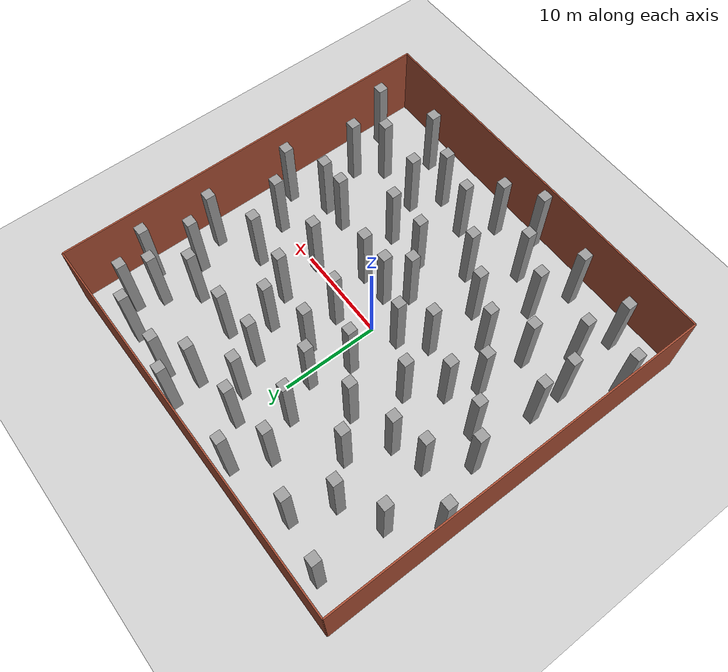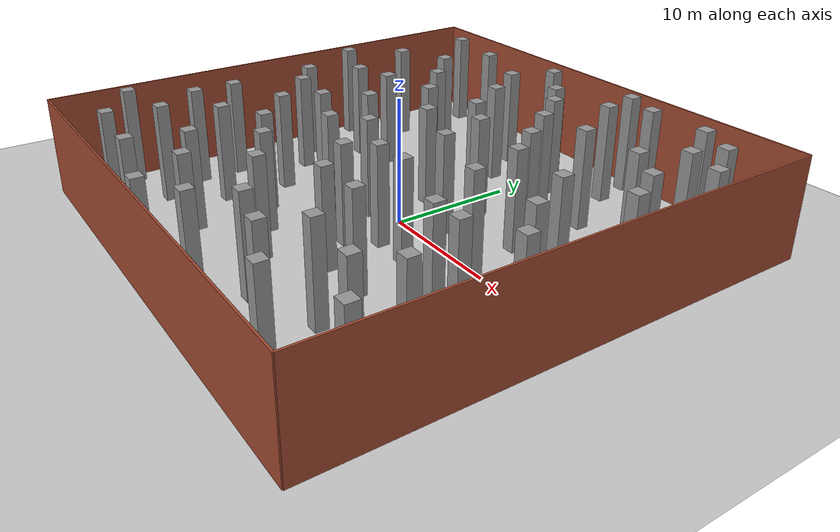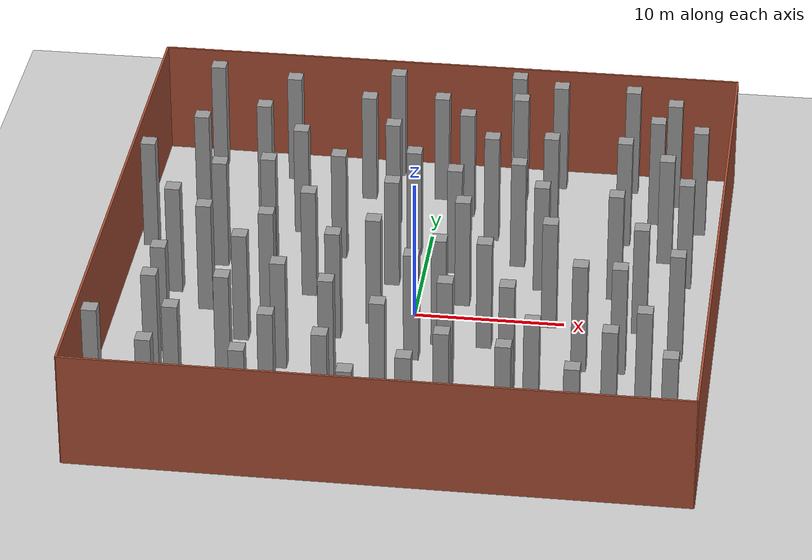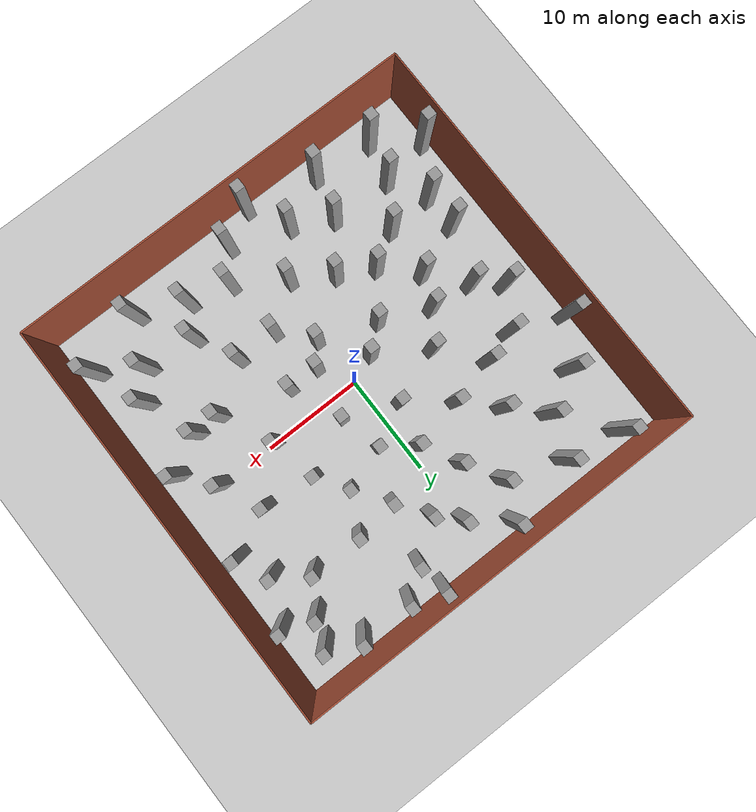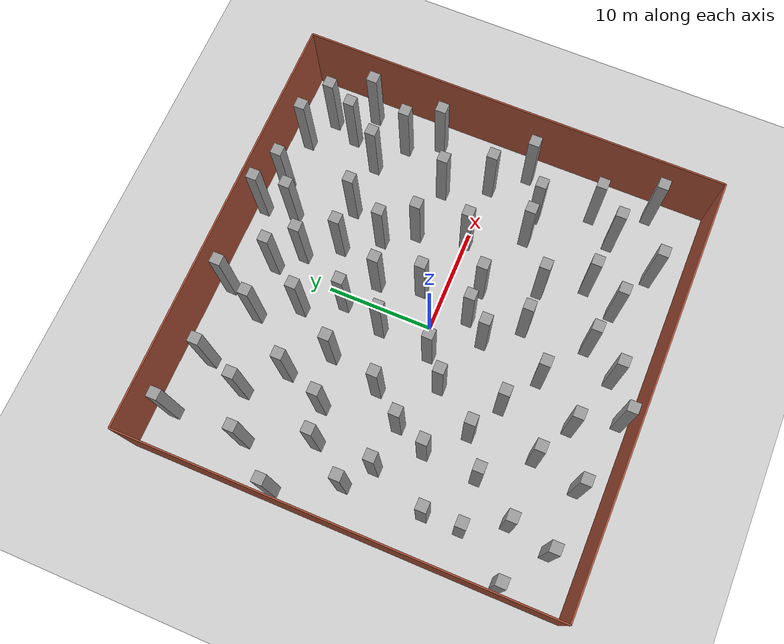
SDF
<sdf version="1.7">
 <world name="default">
  <light name="sun" type="directional">
   <pose>0 0 10 0 -0 0</pose>
   <diffuse>0.8 0.8 0.8 1</diffuse>
   <specular>0.2 0.2 0.2 1</specular>
   <attenuation>
    <range>1000</range>
    <constant>0.9</constant>
    <linear>0.01</linear>
    <quadratic>0.001</quadratic>
   </attenuation>
   <direction>-0.5 0.1 -0.9</direction>
   <spot><inner_angle>0</inner_angle><outer_angle>0</outer_angle><falloff>0</falloff></spot>
  </light>
  <model name="ground_plane">
   <static>1</static>
   <link name="link">
    <collision name="collision">
     <geometry><plane><normal>0 0 1</normal><size>100 100</size></plane></geometry>
     <surface>
      <contact><collide_bitmask>65535</collide_bitmask></contact>
      <friction><ode><mu>100</mu><mu2>50</mu2></ode></friction>
     </surface>
    </collision>
    <visual name="visual">
     <cast_shadows>0</cast_shadows>
     <geometry><plane><normal>0 0 1</normal><size>100 100</size></plane></geometry>
     <material>
      <script><uri>file://media/materials/scripts/gazebo.material</uri><name>Gazebo/Grey</name></script>
     </material>
    </visual>
   </link>
  </model>
  <gravity>0 0 -9.8</gravity>
  <magnetic_field>6e-06 2.3e-05 -4.2e-05</magnetic_field>
  <atmosphere type="adiabatic"/>
  <physics type="ode">
   <max_step_size>0.001</max_step_size>
   <real_time_factor>1</real_time_factor>
   <real_time_update_rate>1000</real_time_update_rate>
  </physics>
  <scene><ambient>0.4 0.4 0.4 1</ambient><background>0.7 0.7 0.7 1</background><shadows>1</shadows></scene>
  <spherical_coordinates>
   <surface_model>EARTH_WGS84</surface_model>
   <latitude_deg>0</latitude_deg>
   <longitude_deg>0</longitude_deg>
   <elevation>0</elevation>
   <heading_deg>0</heading_deg>
  </spherical_coordinates>
  <model name="sim_room_square">
   <link name="Wall_14">
    <collision name="Wall_14_Collision">
     <geometry><box><size>40 0.15 8</size></box></geometry>
     <pose>0 0 4 0 -0 0</pose>
    </collision>
    <visual name="Wall_14_Visual">
     <pose>0 0 4 0 -0 0</pose>
     <geometry><box><size>40 0.15 8</size></box></geometry>
     <material>
      <script><uri>file://media/materials/scripts/gazebo.material</uri><name>Gazebo/Bricks</name></script>
      <ambient>1 1 1 1</ambient>
     </material>
     <meta><layer>0</layer></meta>
    </visual>
    <pose>20 -0 0 0 -0 -1.5708</pose>
   </link>
   <link name="Wall_15">
    <collision name="Wall_15_Collision">
     <geometry><box><size>40 0.15 8</size></box></geometry>
     <pose>0 0 4 0 -0 0</pose>
    </collision>
    <visual name="Wall_15_Visual">
     <pose>0 0 4 0 -0 0</pose>
     <geometry><box><size>40 0.15 8</size></box></geometry>
     <material>
      <script><uri>file://media/materials/scripts/gazebo.material</uri><name>Gazebo/Bricks</name></script>
      <ambient>1 1 1 1</ambient>
     </material>
     <meta><layer>0</layer></meta>
    </visual>
    <pose>0 -20 0 0 -0 3.14159</pose>
   </link>
   <link name="Wall_16">
    <collision name="Wall_16_Collision">
     <geometry><box><size>40 0.15 8</size></box></geometry>
     <pose>0 0 4 0 -0 0</pose>
    </collision>
    <visual name="Wall_16_Visual">
     <pose>0 0 4 0 -0 0</pose>
     <geometry><box><size>40 0.15 8</size></box></geometry>
     <material>
      <script><uri>file://media/materials/scripts/gazebo.material</uri><name>Gazebo/Bricks</name></script>
      <ambient>1 1 1 1</ambient>
     </material>
     <meta><layer>0</layer></meta>
    </visual>
    <pose>-20 -0 0 0 -0 1.5708</pose>
   </link>
   <link name="Wall_19">
    <collision name="Wall_19_Collision">
     <geometry><box><size>40 0.15 8</size></box></geometry>
     <pose>0 0 4 0 -0 0</pose>
    </collision>
    <visual name="Wall_19_Visual">
     <pose>0 0 4 0 -0 0</pose>
     <geometry><box><size>40 0.15 8</size></box></geometry>
     <material>
      <script><uri>file://media/materials/scripts/gazebo.material</uri><name>Gazebo/Bricks</name></script>
      <ambient>1 1 1 1</ambient>
     </material>
     <meta><layer>0</layer></meta>
    </visual>
    <pose>0 20 0 0 -0 0</pose>
   </link>
   <static>1</static>
  </model>
  <model name="unit_box_static">
   <link name="link">
    <inertial>
     <mass>1</mass>
     <inertia>
      <ixx>0.166667</ixx>
      <ixy>0</ixy>
      <ixz>0</ixz>
      <iyy>0.166667</iyy>
      <iyz>0</iyz>
      <izz>0.166667</izz>
     </inertia>
    </inertial>
    <visual name="visual">
     <geometry><box><size>1 1 8</size></box></geometry>
     <material>
      <script><name>Gazebo/Grey</name><uri>file://media/materials/scripts/gazebo.material</uri></script>
      <shader type="pixel"/>
     </material>
    </visual>
    <collision name="collision">
     <geometry><box><size>1 1 8</size></box></geometry>
     <surface>
      <friction>
       <ode><mu>1</mu><mu2>1</mu2><fdir1>0 0 0</fdir1><slip1>0</slip1><slip2>0</slip2></ode>
       <torsional>
        <coefficient>1</coefficient>
        <patch_radius>0</patch_radius>
        <surface_radius>0</surface_radius>
        <use_patch_radius>1</use_patch_radius>
        <ode><slip>0</slip></ode>
       </torsional>
      </friction>
      <bounce><restitution_coefficient>0</restitution_coefficient><threshold>1e+06</threshold></bounce>
      <contact>
       <collide_without_contact>0</collide_without_contact>
       <collide_without_contact_bitmask>1</collide_without_contact_bitmask>
       <collide_bitmask>1</collide_bitmask>
       <ode>
        <soft_cfm>0</soft_cfm>
        <soft_erp>0.2</soft_erp>
        <kp>1e+13</kp>
        <kd>1</kd>
        <max_vel>0.01</max_vel>
        <min_depth>0</min_depth>
       </ode>
       <bullet>
        <split_impulse>1</split_impulse>
        <split_impulse_penetration_threshold>-0.01</split_impulse_penetration_threshold>
        <soft_cfm>0</soft_cfm>
        <soft_erp>0.2</soft_erp>
        <kp>1e+13</kp>
        <kd>1</kd>
       </bullet>
      </contact>
     </surface>
    </collision>
   </link>
   <static>1</static>
   <pose>-2.89298 11.5277 4 0 -0 0</pose>
  </model>
  <model name="unit_box_static_clone">
   <link name="link">
    <inertial>
     <mass>1</mass>
     <inertia>
      <ixx>0.166667</ixx>
      <ixy>0</ixy>
      <ixz>0</ixz>
      <iyy>0.166667</iyy>
      <iyz>0</iyz>
      <izz>0.166667</izz>
     </inertia>
    </inertial>
    <visual name="visual">
     <geometry><box><size>1 1 8</size></box></geometry>
     <material>
      <script><name>Gazebo/Grey</name><uri>file://media/materials/scripts/gazebo.material</uri></script>
      <shader type="pixel"/>
     </material>
    </visual>
    <collision name="collision">
     <geometry><box><size>1 1 8</size></box></geometry>
     <surface>
      <friction>
       <ode><mu>1</mu><mu2>1</mu2><fdir1>0 0 0</fdir1><slip1>0</slip1><slip2>0</slip2></ode>
       <torsional>
        <coefficient>1</coefficient>
        <patch_radius>0</patch_radius>
        <surface_radius>0</surface_radius>
        <use_patch_radius>1</use_patch_radius>
        <ode><slip>0</slip></ode>
       </torsional>
      </friction>
      <bounce><restitution_coefficient>0</restitution_coefficient><threshold>1e+06</threshold></bounce>
      <contact>
       <collide_without_contact>0</collide_without_contact>
       <collide_without_contact_bitmask>1</collide_without_contact_bitmask>
       <collide_bitmask>1</collide_bitmask>
       <ode>
        <soft_cfm>0</soft_cfm>
        <soft_erp>0.2</soft_erp>
        <kp>1e+13</kp>
        <kd>1</kd>
        <max_vel>0.01</max_vel>
        <min_depth>0</min_depth>
       </ode>
       <bullet>
        <split_impulse>1</split_impulse>
        <split_impulse_penetration_threshold>-0.01</split_impulse_penetration_threshold>
        <soft_cfm>0</soft_cfm>
        <soft_erp>0.2</soft_erp>
        <kp>1e+13</kp>
        <kd>1</kd>
       </bullet>
      </contact>
     </surface>
    </collision>
   </link>
   <static>1</static>
   <pose>-1 8 4 0 -0 0</pose>
  </model>
  <model name="unit_box_static_clone_0">
   <link name="link">
    <inertial>
     <mass>1</mass>
     <inertia>
      <ixx>0.166667</ixx>
      <ixy>0</ixy>
      <ixz>0</ixz>
      <iyy>0.166667</iyy>
      <iyz>0</iyz>
      <izz>0.166667</izz>
     </inertia>
    </inertial>
    <visual name="visual">
     <geometry><box><size>1 1 8</size></box></geometry>
     <material>
      <script><name>Gazebo/Grey</name><uri>file://media/materials/scripts/gazebo.material</uri></script>
      <shader type="pixel"/>
     </material>
    </visual>
    <collision name="collision">
     <geometry><box><size>1 1 8</size></box></geometry>
     <surface>
      <friction>
       <ode><mu>1</mu><mu2>1</mu2><fdir1>0 0 0</fdir1><slip1>0</slip1><slip2>0</slip2></ode>
       <torsional>
        <coefficient>1</coefficient>
        <patch_radius>0</patch_radius>
        <surface_radius>0</surface_radius>
        <use_patch_radius>1</use_patch_radius>
        <ode><slip>0</slip></ode>
       </torsional>
      </friction>
      <bounce><restitution_coefficient>0</restitution_coefficient><threshold>1e+06</threshold></bounce>
      <contact>
       <collide_without_contact>0</collide_without_contact>
       <collide_without_contact_bitmask>1</collide_without_contact_bitmask>
       <collide_bitmask>1</collide_bitmask>
       <ode>
        <soft_cfm>0</soft_cfm>
        <soft_erp>0.2</soft_erp>
        <kp>1e+13</kp>
        <kd>1</kd>
        <max_vel>0.01</max_vel>
        <min_depth>0</min_depth>
       </ode>
       <bullet>
        <split_impulse>1</split_impulse>
        <split_impulse_penetration_threshold>-0.01</split_impulse_penetration_threshold>
        <soft_cfm>0</soft_cfm>
        <soft_erp>0.2</soft_erp>
        <kp>1e+13</kp>
        <kd>1</kd>
       </bullet>
      </contact>
     </surface>
    </collision>
   </link>
   <static>1</static>
   <pose>-2 4 4 0 -0 0</pose>
  </model>
  <model name="unit_box_static_clone_1">
   <link name="link">
    <inertial>
     <mass>1</mass>
     <inertia>
      <ixx>0.166667</ixx>
      <ixy>0</ixy>
      <ixz>0</ixz>
      <iyy>0.166667</iyy>
      <iyz>0</iyz>
      <izz>0.166667</izz>
     </inertia>
    </inertial>
    <visual name="visual">
     <geometry><box><size>1 1 8</size></box></geometry>
     <material>
      <script><name>Gazebo/Grey</name><uri>file://media/materials/scripts/gazebo.material</uri></script>
      <shader type="pixel"/>
     </material>
    </visual>
    <collision name="collision">
     <geometry><box><size>1 1 8</size></box></geometry>
     <surface>
      <friction>
       <ode><mu>1</mu><mu2>1</mu2><fdir1>0 0 0</fdir1><slip1>0</slip1><slip2>0</slip2></ode>
       <torsional>
        <coefficient>1</coefficient>
        <patch_radius>0</patch_radius>
        <surface_radius>0</surface_radius>
        <use_patch_radius>1</use_patch_radius>
        <ode><slip>0</slip></ode>
       </torsional>
      </friction>
      <bounce><restitution_coefficient>0</restitution_coefficient><threshold>1e+06</threshold></bounce>
      <contact>
       <collide_without_contact>0</collide_without_contact>
       <collide_without_contact_bitmask>1</collide_without_contact_bitmask>
       <collide_bitmask>1</collide_bitmask>
       <ode>
        <soft_cfm>0</soft_cfm>
        <soft_erp>0.2</soft_erp>
        <kp>1e+13</kp>
        <kd>1</kd>
        <max_vel>0.01</max_vel>
        <min_depth>0</min_depth>
       </ode>
       <bullet>
        <split_impulse>1</split_impulse>
        <split_impulse_penetration_threshold>-0.01</split_impulse_penetration_threshold>
        <soft_cfm>0</soft_cfm>
        <soft_erp>0.2</soft_erp>
        <kp>1e+13</kp>
        <kd>1</kd>
       </bullet>
      </contact>
     </surface>
    </collision>
   </link>
   <static>1</static>
   <pose>-7.32735 2 4 0 -0 0</pose>
  </model>
  <model name="unit_box_static_clone_2">
   <link name="link">
    <inertial>
     <mass>1</mass>
     <inertia>
      <ixx>0.166667</ixx>
      <ixy>0</ixy>
      <ixz>0</ixz>
      <iyy>0.166667</iyy>
      <iyz>0</iyz>
      <izz>0.166667</izz>
     </inertia>
    </inertial>
    <visual name="visual">
     <geometry><box><size>1 1 8</size></box></geometry>
     <material>
      <script><name>Gazebo/Grey</name><uri>file://media/materials/scripts/gazebo.material</uri></script>
      <shader type="pixel"/>
     </material>
    </visual>
    <collision name="collision">
     <geometry><box><size>1 1 8</size></box></geometry>
     <surface>
      <friction>
       <ode><mu>1</mu><mu2>1</mu2><fdir1>0 0 0</fdir1><slip1>0</slip1><slip2>0</slip2></ode>
       <torsional>
        <coefficient>1</coefficient>
        <patch_radius>0</patch_radius>
        <surface_radius>0</surface_radius>
        <use_patch_radius>1</use_patch_radius>
        <ode><slip>0</slip></ode>
       </torsional>
      </friction>
      <bounce><restitution_coefficient>0</restitution_coefficient><threshold>1e+06</threshold></bounce>
      <contact>
       <collide_without_contact>0</collide_without_contact>
       <collide_without_contact_bitmask>1</collide_without_contact_bitmask>
       <collide_bitmask>1</collide_bitmask>
       <ode>
        <soft_cfm>0</soft_cfm>
        <soft_erp>0.2</soft_erp>
        <kp>1e+13</kp>
        <kd>1</kd>
        <max_vel>0.01</max_vel>
        <min_depth>0</min_depth>
       </ode>
       <bullet>
        <split_impulse>1</split_impulse>
        <split_impulse_penetration_threshold>-0.01</split_impulse_penetration_threshold>
        <soft_cfm>0</soft_cfm>
        <soft_erp>0.2</soft_erp>
        <kp>1e+13</kp>
        <kd>1</kd>
       </bullet>
      </contact>
     </surface>
    </collision>
   </link>
   <static>1</static>
   <pose>-10.6403 5.9324 4 0 -0 0</pose>
  </model>
  <model name="unit_box_static_clone_3">
   <link name="link">
    <inertial>
     <mass>1</mass>
     <inertia>
      <ixx>0.166667</ixx>
      <ixy>0</ixy>
      <ixz>0</ixz>
      <iyy>0.166667</iyy>
      <iyz>0</iyz>
      <izz>0.166667</izz>
     </inertia>
    </inertial>
    <visual name="visual">
     <geometry><box><size>1 1 8</size></box></geometry>
     <material>
      <script><name>Gazebo/Grey</name><uri>file://media/materials/scripts/gazebo.material</uri></script>
      <shader type="pixel"/>
     </material>
    </visual>
    <collision name="collision">
     <geometry><box><size>1 1 8</size></box></geometry>
     <surface>
      <friction>
       <ode><mu>1</mu><mu2>1</mu2><fdir1>0 0 0</fdir1><slip1>0</slip1><slip2>0</slip2></ode>
       <torsional>
        <coefficient>1</coefficient>
        <patch_radius>0</patch_radius>
        <surface_radius>0</surface_radius>
        <use_patch_radius>1</use_patch_radius>
        <ode><slip>0</slip></ode>
       </torsional>
      </friction>
      <bounce><restitution_coefficient>0</restitution_coefficient><threshold>1e+06</threshold></bounce>
      <contact>
       <collide_without_contact>0</collide_without_contact>
       <collide_without_contact_bitmask>1</collide_without_contact_bitmask>
       <collide_bitmask>1</collide_bitmask>
       <ode>
        <soft_cfm>0</soft_cfm>
        <soft_erp>0.2</soft_erp>
        <kp>1e+13</kp>
        <kd>1</kd>
        <max_vel>0.01</max_vel>
        <min_depth>0</min_depth>
       </ode>
       <bullet>
        <split_impulse>1</split_impulse>
        <split_impulse_penetration_threshold>-0.01</split_impulse_penetration_threshold>
        <soft_cfm>0</soft_cfm>
        <soft_erp>0.2</soft_erp>
        <kp>1e+13</kp>
        <kd>1</kd>
       </bullet>
      </contact>
     </surface>
    </collision>
   </link>
   <static>1</static>
   <pose>-13.8066 5.02416 4 0 -0 0</pose>
  </model>
  <model name="unit_box_static_clone_4">
   <link name="link">
    <inertial>
     <mass>1</mass>
     <inertia>
      <ixx>0.166667</ixx>
      <ixy>0</ixy>
      <ixz>0</ixz>
      <iyy>0.166667</iyy>
      <iyz>0</iyz>
      <izz>0.166667</izz>
     </inertia>
    </inertial>
    <visual name="visual">
     <geometry><box><size>1 1 8</size></box></geometry>
     <material>
      <script><name>Gazebo/Grey</name><uri>file://media/materials/scripts/gazebo.material</uri></script>
      <shader type="pixel"/>
     </material>
    </visual>
    <collision name="collision">
     <geometry><box><size>1 1 8</size></box></geometry>
     <surface>
      <friction>
       <ode><mu>1</mu><mu2>1</mu2><fdir1>0 0 0</fdir1><slip1>0</slip1><slip2>0</slip2></ode>
       <torsional>
        <coefficient>1</coefficient>
        <patch_radius>0</patch_radius>
        <surface_radius>0</surface_radius>
        <use_patch_radius>1</use_patch_radius>
        <ode><slip>0</slip></ode>
       </torsional>
      </friction>
      <bounce><restitution_coefficient>0</restitution_coefficient><threshold>1e+06</threshold></bounce>
      <contact>
       <collide_without_contact>0</collide_without_contact>
       <collide_without_contact_bitmask>1</collide_without_contact_bitmask>
       <collide_bitmask>1</collide_bitmask>
       <ode>
        <soft_cfm>0</soft_cfm>
        <soft_erp>0.2</soft_erp>
        <kp>1e+13</kp>
        <kd>1</kd>
        <max_vel>0.01</max_vel>
        <min_depth>0</min_depth>
       </ode>
       <bullet>
        <split_impulse>1</split_impulse>
        <split_impulse_penetration_threshold>-0.01</split_impulse_penetration_threshold>
        <soft_cfm>0</soft_cfm>
        <soft_erp>0.2</soft_erp>
        <kp>1e+13</kp>
        <kd>1</kd>
       </bullet>
      </contact>
     </surface>
    </collision>
   </link>
   <static>1</static>
   <pose>-11 -4 4 0 -0 0</pose>
  </model>
  <model name="unit_box_static_clone_5">
   <link name="link">
    <inertial>
     <mass>1</mass>
     <inertia>
      <ixx>0.166667</ixx>
      <ixy>0</ixy>
      <ixz>0</ixz>
      <iyy>0.166667</iyy>
      <iyz>0</iyz>
      <izz>0.166667</izz>
     </inertia>
    </inertial>
    <visual name="visual">
     <geometry><box><size>1 1 8</size></box></geometry>
     <material>
      <script><name>Gazebo/Grey</name><uri>file://media/materials/scripts/gazebo.material</uri></script>
      <shader type="pixel"/>
     </material>
    </visual>
    <collision name="collision">
     <geometry><box><size>1 1 8</size></box></geometry>
     <surface>
      <friction>
       <ode><mu>1</mu><mu2>1</mu2><fdir1>0 0 0</fdir1><slip1>0</slip1><slip2>0</slip2></ode>
       <torsional>
        <coefficient>1</coefficient>
        <patch_radius>0</patch_radius>
        <surface_radius>0</surface_radius>
        <use_patch_radius>1</use_patch_radius>
        <ode><slip>0</slip></ode>
       </torsional>
      </friction>
      <bounce><restitution_coefficient>0</restitution_coefficient><threshold>1e+06</threshold></bounce>
      <contact>
       <collide_without_contact>0</collide_without_contact>
       <collide_without_contact_bitmask>1</collide_without_contact_bitmask>
       <collide_bitmask>1</collide_bitmask>
       <ode>
        <soft_cfm>0</soft_cfm>
        <soft_erp>0.2</soft_erp>
        <kp>1e+13</kp>
        <kd>1</kd>
        <max_vel>0.01</max_vel>
        <min_depth>0</min_depth>
       </ode>
       <bullet>
        <split_impulse>1</split_impulse>
        <split_impulse_penetration_threshold>-0.01</split_impulse_penetration_threshold>
        <soft_cfm>0</soft_cfm>
        <soft_erp>0.2</soft_erp>
        <kp>1e+13</kp>
        <kd>1</kd>
       </bullet>
      </contact>
     </surface>
    </collision>
   </link>
   <static>1</static>
   <pose>-9.69968 -1.00435 4 0 -0 0</pose>
  </model>
  <model name="unit_box_static_clone_6">
   <link name="link">
    <inertial>
     <mass>1</mass>
     <inertia>
      <ixx>0.166667</ixx>
      <ixy>0</ixy>
      <ixz>0</ixz>
      <iyy>0.166667</iyy>
      <iyz>0</iyz>
      <izz>0.166667</izz>
     </inertia>
    </inertial>
    <visual name="visual">
     <geometry><box><size>1 1 8</size></box></geometry>
     <material>
      <script><name>Gazebo/Grey</name><uri>file://media/materials/scripts/gazebo.material</uri></script>
      <shader type="pixel"/>
     </material>
    </visual>
    <collision name="collision">
     <geometry><box><size>1 1 8</size></box></geometry>
     <surface>
      <friction>
       <ode><mu>1</mu><mu2>1</mu2><fdir1>0 0 0</fdir1><slip1>0</slip1><slip2>0</slip2></ode>
       <torsional>
        <coefficient>1</coefficient>
        <patch_radius>0</patch_radius>
        <surface_radius>0</surface_radius>
        <use_patch_radius>1</use_patch_radius>
        <ode><slip>0</slip></ode>
       </torsional>
      </friction>
      <bounce><restitution_coefficient>0</restitution_coefficient><threshold>1e+06</threshold></bounce>
      <contact>
       <collide_without_contact>0</collide_without_contact>
       <collide_without_contact_bitmask>1</collide_without_contact_bitmask>
       <collide_bitmask>1</collide_bitmask>
       <ode>
        <soft_cfm>0</soft_cfm>
        <soft_erp>0.2</soft_erp>
        <kp>1e+13</kp>
        <kd>1</kd>
        <max_vel>0.01</max_vel>
        <min_depth>0</min_depth>
       </ode>
       <bullet>
        <split_impulse>1</split_impulse>
        <split_impulse_penetration_threshold>-0.01</split_impulse_penetration_threshold>
        <soft_cfm>0</soft_cfm>
        <soft_erp>0.2</soft_erp>
        <kp>1e+13</kp>
        <kd>1</kd>
       </bullet>
      </contact>
     </surface>
    </collision>
   </link>
   <static>1</static>
   <pose>-5 -3 4 0 -0 0</pose>
  </model>
  <model name="unit_box_static_clone_7">
   <link name="link">
    <inertial>
     <mass>1</mass>
     <inertia>
      <ixx>0.166667</ixx>
      <ixy>0</ixy>
      <ixz>0</ixz>
      <iyy>0.166667</iyy>
      <iyz>0</iyz>
      <izz>0.166667</izz>
     </inertia>
    </inertial>
    <visual name="visual">
     <geometry><box><size>1 1 8</size></box></geometry>
     <material>
      <script><name>Gazebo/Grey</name><uri>file://media/materials/scripts/gazebo.material</uri></script>
      <shader type="pixel"/>
     </material>
    </visual>
    <collision name="collision">
     <geometry><box><size>1 1 8</size></box></geometry>
     <surface>
      <friction>
       <ode><mu>1</mu><mu2>1</mu2><fdir1>0 0 0</fdir1><slip1>0</slip1><slip2>0</slip2></ode>
       <torsional>
        <coefficient>1</coefficient>
        <patch_radius>0</patch_radius>
        <surface_radius>0</surface_radius>
        <use_patch_radius>1</use_patch_radius>
        <ode><slip>0</slip></ode>
       </torsional>
      </friction>
      <bounce><restitution_coefficient>0</restitution_coefficient><threshold>1e+06</threshold></bounce>
      <contact>
       <collide_without_contact>0</collide_without_contact>
       <collide_without_contact_bitmask>1</collide_without_contact_bitmask>
       <collide_bitmask>1</collide_bitmask>
       <ode>
        <soft_cfm>0</soft_cfm>
        <soft_erp>0.2</soft_erp>
        <kp>1e+13</kp>
        <kd>1</kd>
        <max_vel>0.01</max_vel>
        <min_depth>0</min_depth>
       </ode>
       <bullet>
        <split_impulse>1</split_impulse>
        <split_impulse_penetration_threshold>-0.01</split_impulse_penetration_threshold>
        <soft_cfm>0</soft_cfm>
        <soft_erp>0.2</soft_erp>
        <kp>1e+13</kp>
        <kd>1</kd>
       </bullet>
      </contact>
     </surface>
    </collision>
   </link>
   <static>1</static>
   <pose>-2.58663 -1 4 0 -0 0</pose>
  </model>
  <model name="unit_box_static_clone_8">
   <link name="link">
    <inertial>
     <mass>1</mass>
     <inertia>
      <ixx>0.166667</ixx>
      <ixy>0</ixy>
      <ixz>0</ixz>
      <iyy>0.166667</iyy>
      <iyz>0</iyz>
      <izz>0.166667</izz>
     </inertia>
    </inertial>
    <visual name="visual">
     <geometry><box><size>1 1 8</size></box></geometry>
     <material>
      <script><name>Gazebo/Grey</name><uri>file://media/materials/scripts/gazebo.material</uri></script>
      <shader type="pixel"/>
     </material>
    </visual>
    <collision name="collision">
     <geometry><box><size>1 1 8</size></box></geometry>
     <surface>
      <friction>
       <ode><mu>1</mu><mu2>1</mu2><fdir1>0 0 0</fdir1><slip1>0</slip1><slip2>0</slip2></ode>
       <torsional>
        <coefficient>1</coefficient>
        <patch_radius>0</patch_radius>
        <surface_radius>0</surface_radius>
        <use_patch_radius>1</use_patch_radius>
        <ode><slip>0</slip></ode>
       </torsional>
      </friction>
      <bounce><restitution_coefficient>0</restitution_coefficient><threshold>1e+06</threshold></bounce>
      <contact>
       <collide_without_contact>0</collide_without_contact>
       <collide_without_contact_bitmask>1</collide_without_contact_bitmask>
       <collide_bitmask>1</collide_bitmask>
       <ode>
        <soft_cfm>0</soft_cfm>
        <soft_erp>0.2</soft_erp>
        <kp>1e+13</kp>
        <kd>1</kd>
        <max_vel>0.01</max_vel>
        <min_depth>0</min_depth>
       </ode>
       <bullet>
        <split_impulse>1</split_impulse>
        <split_impulse_penetration_threshold>-0.01</split_impulse_penetration_threshold>
        <soft_cfm>0</soft_cfm>
        <soft_erp>0.2</soft_erp>
        <kp>1e+13</kp>
        <kd>1</kd>
       </bullet>
      </contact>
     </surface>
    </collision>
   </link>
   <static>1</static>
   <pose>0.430119 -5 4 0 -0 0</pose>
  </model>
  <model name="unit_box_static_clone_9">
   <link name="link">
    <inertial>
     <mass>1</mass>
     <inertia>
      <ixx>0.166667</ixx>
      <ixy>0</ixy>
      <ixz>0</ixz>
      <iyy>0.166667</iyy>
      <iyz>0</iyz>
      <izz>0.166667</izz>
     </inertia>
    </inertial>
    <visual name="visual">
     <geometry><box><size>1 1 8</size></box></geometry>
     <material>
      <script><name>Gazebo/Grey</name><uri>file://media/materials/scripts/gazebo.material</uri></script>
      <shader type="pixel"/>
     </material>
    </visual>
    <collision name="collision">
     <geometry><box><size>1 1 8</size></box></geometry>
     <surface>
      <friction>
       <ode><mu>1</mu><mu2>1</mu2><fdir1>0 0 0</fdir1><slip1>0</slip1><slip2>0</slip2></ode>
       <torsional>
        <coefficient>1</coefficient>
        <patch_radius>0</patch_radius>
        <surface_radius>0</surface_radius>
        <use_patch_radius>1</use_patch_radius>
        <ode><slip>0</slip></ode>
       </torsional>
      </friction>
      <bounce><restitution_coefficient>0</restitution_coefficient><threshold>1e+06</threshold></bounce>
      <contact>
       <collide_without_contact>0</collide_without_contact>
       <collide_without_contact_bitmask>1</collide_without_contact_bitmask>
       <collide_bitmask>1</collide_bitmask>
       <ode>
        <soft_cfm>0</soft_cfm>
        <soft_erp>0.2</soft_erp>
        <kp>1e+13</kp>
        <kd>1</kd>
        <max_vel>0.01</max_vel>
        <min_depth>0</min_depth>
       </ode>
       <bullet>
        <split_impulse>1</split_impulse>
        <split_impulse_penetration_threshold>-0.01</split_impulse_penetration_threshold>
        <soft_cfm>0</soft_cfm>
        <soft_erp>0.2</soft_erp>
        <kp>1e+13</kp>
        <kd>1</kd>
       </bullet>
      </contact>
     </surface>
    </collision>
   </link>
   <static>1</static>
   <pose>3 2 4 0 -0 0</pose>
  </model>
  <model name="unit_box_static_clone_10">
   <link name="link">
    <inertial>
     <mass>1</mass>
     <inertia>
      <ixx>0.166667</ixx>
      <ixy>0</ixy>
      <ixz>0</ixz>
      <iyy>0.166667</iyy>
      <iyz>0</iyz>
      <izz>0.166667</izz>
     </inertia>
    </inertial>
    <visual name="visual">
     <geometry><box><size>1 1 8</size></box></geometry>
     <material>
      <script><name>Gazebo/Grey</name><uri>file://media/materials/scripts/gazebo.material</uri></script>
      <shader type="pixel"/>
     </material>
    </visual>
    <collision name="collision">
     <geometry><box><size>1 1 8</size></box></geometry>
     <surface>
      <friction>
       <ode><mu>1</mu><mu2>1</mu2><fdir1>0 0 0</fdir1><slip1>0</slip1><slip2>0</slip2></ode>
       <torsional>
        <coefficient>1</coefficient>
        <patch_radius>0</patch_radius>
        <surface_radius>0</surface_radius>
        <use_patch_radius>1</use_patch_radius>
        <ode><slip>0</slip></ode>
       </torsional>
      </friction>
      <bounce><restitution_coefficient>0</restitution_coefficient><threshold>1e+06</threshold></bounce>
      <contact>
       <collide_without_contact>0</collide_without_contact>
       <collide_without_contact_bitmask>1</collide_without_contact_bitmask>
       <collide_bitmask>1</collide_bitmask>
       <ode>
        <soft_cfm>0</soft_cfm>
        <soft_erp>0.2</soft_erp>
        <kp>1e+13</kp>
        <kd>1</kd>
        <max_vel>0.01</max_vel>
        <min_depth>0</min_depth>
       </ode>
       <bullet>
        <split_impulse>1</split_impulse>
        <split_impulse_penetration_threshold>-0.01</split_impulse_penetration_threshold>
        <soft_cfm>0</soft_cfm>
        <soft_erp>0.2</soft_erp>
        <kp>1e+13</kp>
        <kd>1</kd>
       </bullet>
      </contact>
     </surface>
    </collision>
   </link>
   <static>1</static>
   <pose>5 -3 4 0 -0 0</pose>
  </model>
  <model name="unit_box_static_clone_11">
   <link name="link">
    <inertial>
     <mass>1</mass>
     <inertia>
      <ixx>0.166667</ixx>
      <ixy>0</ixy>
      <ixz>0</ixz>
      <iyy>0.166667</iyy>
      <iyz>0</iyz>
      <izz>0.166667</izz>
     </inertia>
    </inertial>
    <visual name="visual">
     <geometry><box><size>1 1 8</size></box></geometry>
     <material>
      <script><name>Gazebo/Grey</name><uri>file://media/materials/scripts/gazebo.material</uri></script>
      <shader type="pixel"/>
     </material>
    </visual>
    <collision name="collision">
     <geometry><box><size>1 1 8</size></box></geometry>
     <surface>
      <friction>
       <ode><mu>1</mu><mu2>1</mu2><fdir1>0 0 0</fdir1><slip1>0</slip1><slip2>0</slip2></ode>
       <torsional>
        <coefficient>1</coefficient>
        <patch_radius>0</patch_radius>
        <surface_radius>0</surface_radius>
        <use_patch_radius>1</use_patch_radius>
        <ode><slip>0</slip></ode>
       </torsional>
      </friction>
      <bounce><restitution_coefficient>0</restitution_coefficient><threshold>1e+06</threshold></bounce>
      <contact>
       <collide_without_contact>0</collide_without_contact>
       <collide_without_contact_bitmask>1</collide_without_contact_bitmask>
       <collide_bitmask>1</collide_bitmask>
       <ode>
        <soft_cfm>0</soft_cfm>
        <soft_erp>0.2</soft_erp>
        <kp>1e+13</kp>
        <kd>1</kd>
        <max_vel>0.01</max_vel>
        <min_depth>0</min_depth>
       </ode>
       <bullet>
        <split_impulse>1</split_impulse>
        <split_impulse_penetration_threshold>-0.01</split_impulse_penetration_threshold>
        <soft_cfm>0</soft_cfm>
        <soft_erp>0.2</soft_erp>
        <kp>1e+13</kp>
        <kd>1</kd>
       </bullet>
      </contact>
     </surface>
    </collision>
   </link>
   <static>1</static>
   <pose>8 4.54489 4 0 -0 0</pose>
  </model>
  <model name="unit_box_static_clone_12">
   <link name="link">
    <inertial>
     <mass>1</mass>
     <inertia>
      <ixx>0.166667</ixx>
      <ixy>0</ixy>
      <ixz>0</ixz>
      <iyy>0.166667</iyy>
      <iyz>0</iyz>
      <izz>0.166667</izz>
     </inertia>
    </inertial>
    <visual name="visual">
     <geometry><box><size>1 1 8</size></box></geometry>
     <material>
      <script><name>Gazebo/Grey</name><uri>file://media/materials/scripts/gazebo.material</uri></script>
      <shader type="pixel"/>
     </material>
    </visual>
    <collision name="collision">
     <geometry><box><size>1 1 8</size></box></geometry>
     <surface>
      <friction>
       <ode><mu>1</mu><mu2>1</mu2><fdir1>0 0 0</fdir1><slip1>0</slip1><slip2>0</slip2></ode>
       <torsional>
        <coefficient>1</coefficient>
        <patch_radius>0</patch_radius>
        <surface_radius>0</surface_radius>
        <use_patch_radius>1</use_patch_radius>
        <ode><slip>0</slip></ode>
       </torsional>
      </friction>
      <bounce><restitution_coefficient>0</restitution_coefficient><threshold>1e+06</threshold></bounce>
      <contact>
       <collide_without_contact>0</collide_without_contact>
       <collide_without_contact_bitmask>1</collide_without_contact_bitmask>
       <collide_bitmask>1</collide_bitmask>
       <ode>
        <soft_cfm>0</soft_cfm>
        <soft_erp>0.2</soft_erp>
        <kp>1e+13</kp>
        <kd>1</kd>
        <max_vel>0.01</max_vel>
        <min_depth>0</min_depth>
       </ode>
       <bullet>
        <split_impulse>1</split_impulse>
        <split_impulse_penetration_threshold>-0.01</split_impulse_penetration_threshold>
        <soft_cfm>0</soft_cfm>
        <soft_erp>0.2</soft_erp>
        <kp>1e+13</kp>
        <kd>1</kd>
       </bullet>
      </contact>
     </surface>
    </collision>
   </link>
   <static>1</static>
   <pose>11.4362 -5 4 0 -0 0</pose>
  </model>
  <model name="unit_box_static_clone_13">
   <link name="link">
    <inertial>
     <mass>1</mass>
     <inertia>
      <ixx>0.166667</ixx>
      <ixy>0</ixy>
      <ixz>0</ixz>
      <iyy>0.166667</iyy>
      <iyz>0</iyz>
      <izz>0.166667</izz>
     </inertia>
    </inertial>
    <visual name="visual">
     <geometry><box><size>1 1 8</size></box></geometry>
     <material>
      <script><name>Gazebo/Grey</name><uri>file://media/materials/scripts/gazebo.material</uri></script>
      <shader type="pixel"/>
     </material>
    </visual>
    <collision name="collision">
     <geometry><box><size>1 1 8</size></box></geometry>
     <surface>
      <friction>
       <ode><mu>1</mu><mu2>1</mu2><fdir1>0 0 0</fdir1><slip1>0</slip1><slip2>0</slip2></ode>
       <torsional>
        <coefficient>1</coefficient>
        <patch_radius>0</patch_radius>
        <surface_radius>0</surface_radius>
        <use_patch_radius>1</use_patch_radius>
        <ode><slip>0</slip></ode>
       </torsional>
      </friction>
      <bounce><restitution_coefficient>0</restitution_coefficient><threshold>1e+06</threshold></bounce>
      <contact>
       <collide_without_contact>0</collide_without_contact>
       <collide_without_contact_bitmask>1</collide_without_contact_bitmask>
       <collide_bitmask>1</collide_bitmask>
       <ode>
        <soft_cfm>0</soft_cfm>
        <soft_erp>0.2</soft_erp>
        <kp>1e+13</kp>
        <kd>1</kd>
        <max_vel>0.01</max_vel>
        <min_depth>0</min_depth>
       </ode>
       <bullet>
        <split_impulse>1</split_impulse>
        <split_impulse_penetration_threshold>-0.01</split_impulse_penetration_threshold>
        <soft_cfm>0</soft_cfm>
        <soft_erp>0.2</soft_erp>
        <kp>1e+13</kp>
        <kd>1</kd>
       </bullet>
      </contact>
     </surface>
    </collision>
   </link>
   <static>1</static>
   <pose>15 0 4 0 -0 0</pose>
  </model>
  <model name="unit_box_static_clone_14">
   <link name="link">
    <inertial>
     <mass>1</mass>
     <inertia>
      <ixx>0.166667</ixx>
      <ixy>0</ixy>
      <ixz>0</ixz>
      <iyy>0.166667</iyy>
      <iyz>0</iyz>
      <izz>0.166667</izz>
     </inertia>
    </inertial>
    <visual name="visual">
     <geometry><box><size>1 1 8</size></box></geometry>
     <material>
      <script><name>Gazebo/Grey</name><uri>file://media/materials/scripts/gazebo.material</uri></script>
      <shader type="pixel"/>
     </material>
    </visual>
    <collision name="collision">
     <geometry><box><size>1 1 8</size></box></geometry>
     <surface>
      <friction>
       <ode><mu>1</mu><mu2>1</mu2><fdir1>0 0 0</fdir1><slip1>0</slip1><slip2>0</slip2></ode>
       <torsional>
        <coefficient>1</coefficient>
        <patch_radius>0</patch_radius>
        <surface_radius>0</surface_radius>
        <use_patch_radius>1</use_patch_radius>
        <ode><slip>0</slip></ode>
       </torsional>
      </friction>
      <bounce><restitution_coefficient>0</restitution_coefficient><threshold>1e+06</threshold></bounce>
      <contact>
       <collide_without_contact>0</collide_without_contact>
       <collide_without_contact_bitmask>1</collide_without_contact_bitmask>
       <collide_bitmask>1</collide_bitmask>
       <ode>
        <soft_cfm>0</soft_cfm>
        <soft_erp>0.2</soft_erp>
        <kp>1e+13</kp>
        <kd>1</kd>
        <max_vel>0.01</max_vel>
        <min_depth>0</min_depth>
       </ode>
       <bullet>
        <split_impulse>1</split_impulse>
        <split_impulse_penetration_threshold>-0.01</split_impulse_penetration_threshold>
        <soft_cfm>0</soft_cfm>
        <soft_erp>0.2</soft_erp>
        <kp>1e+13</kp>
        <kd>1</kd>
       </bullet>
      </contact>
     </surface>
    </collision>
   </link>
   <static>1</static>
   <pose>9 0 4 0 -0 0</pose>
  </model>
  <model name="unit_box_static_clone_15">
   <link name="link">
    <inertial>
     <mass>1</mass>
     <inertia>
      <ixx>0.166667</ixx>
      <ixy>0</ixy>
      <ixz>0</ixz>
      <iyy>0.166667</iyy>
      <iyz>0</iyz>
      <izz>0.166667</izz>
     </inertia>
    </inertial>
    <visual name="visual">
     <geometry><box><size>1 1 8</size></box></geometry>
     <material>
      <script><name>Gazebo/Grey</name><uri>file://media/materials/scripts/gazebo.material</uri></script>
      <shader type="pixel"/>
     </material>
    </visual>
    <collision name="collision">
     <geometry><box><size>1 1 8</size></box></geometry>
     <surface>
      <friction>
       <ode><mu>1</mu><mu2>1</mu2><fdir1>0 0 0</fdir1><slip1>0</slip1><slip2>0</slip2></ode>
       <torsional>
        <coefficient>1</coefficient>
        <patch_radius>0</patch_radius>
        <surface_radius>0</surface_radius>
        <use_patch_radius>1</use_patch_radius>
        <ode><slip>0</slip></ode>
       </torsional>
      </friction>
      <bounce><restitution_coefficient>0</restitution_coefficient><threshold>1e+06</threshold></bounce>
      <contact>
       <collide_without_contact>0</collide_without_contact>
       <collide_without_contact_bitmask>1</collide_without_contact_bitmask>
       <collide_bitmask>1</collide_bitmask>
       <ode>
        <soft_cfm>0</soft_cfm>
        <soft_erp>0.2</soft_erp>
        <kp>1e+13</kp>
        <kd>1</kd>
        <max_vel>0.01</max_vel>
        <min_depth>0</min_depth>
       </ode>
       <bullet>
        <split_impulse>1</split_impulse>
        <split_impulse_penetration_threshold>-0.01</split_impulse_penetration_threshold>
        <soft_cfm>0</soft_cfm>
        <soft_erp>0.2</soft_erp>
        <kp>1e+13</kp>
        <kd>1</kd>
       </bullet>
      </contact>
     </surface>
    </collision>
   </link>
   <static>1</static>
   <pose>7 -8 4 0 -0 0</pose>
  </model>
  <model name="unit_box_static_clone_16">
   <link name="link">
    <inertial>
     <mass>1</mass>
     <inertia>
      <ixx>0.166667</ixx>
      <ixy>0</ixy>
      <ixz>0</ixz>
      <iyy>0.166667</iyy>
      <iyz>0</iyz>
      <izz>0.166667</izz>
     </inertia>
    </inertial>
    <visual name="visual">
     <geometry><box><size>1 1 8</size></box></geometry>
     <material>
      <script><name>Gazebo/Grey</name><uri>file://media/materials/scripts/gazebo.material</uri></script>
      <shader type="pixel"/>
     </material>
    </visual>
    <collision name="collision">
     <geometry><box><size>1 1 8</size></box></geometry>
     <surface>
      <friction>
       <ode><mu>1</mu><mu2>1</mu2><fdir1>0 0 0</fdir1><slip1>0</slip1><slip2>0</slip2></ode>
       <torsional>
        <coefficient>1</coefficient>
        <patch_radius>0</patch_radius>
        <surface_radius>0</surface_radius>
        <use_patch_radius>1</use_patch_radius>
        <ode><slip>0</slip></ode>
       </torsional>
      </friction>
      <bounce><restitution_coefficient>0</restitution_coefficient><threshold>1e+06</threshold></bounce>
      <contact>
       <collide_without_contact>0</collide_without_contact>
       <collide_without_contact_bitmask>1</collide_without_contact_bitmask>
       <collide_bitmask>1</collide_bitmask>
       <ode>
        <soft_cfm>0</soft_cfm>
        <soft_erp>0.2</soft_erp>
        <kp>1e+13</kp>
        <kd>1</kd>
        <max_vel>0.01</max_vel>
        <min_depth>0</min_depth>
       </ode>
       <bullet>
        <split_impulse>1</split_impulse>
        <split_impulse_penetration_threshold>-0.01</split_impulse_penetration_threshold>
        <soft_cfm>0</soft_cfm>
        <soft_erp>0.2</soft_erp>
        <kp>1e+13</kp>
        <kd>1</kd>
       </bullet>
      </contact>
     </surface>
    </collision>
   </link>
   <static>1</static>
   <pose>3 -8 4 0 -0 0</pose>
  </model>
  <model name="unit_box_static_clone_17">
   <link name="link">
    <inertial>
     <mass>1</mass>
     <inertia>
      <ixx>0.166667</ixx>
      <ixy>0</ixy>
      <ixz>0</ixz>
      <iyy>0.166667</iyy>
      <iyz>0</iyz>
      <izz>0.166667</izz>
     </inertia>
    </inertial>
    <visual name="visual">
     <geometry><box><size>1 1 8</size></box></geometry>
     <material>
      <script><name>Gazebo/Grey</name><uri>file://media/materials/scripts/gazebo.material</uri></script>
      <shader type="pixel"/>
     </material>
    </visual>
    <collision name="collision">
     <geometry><box><size>1 1 8</size></box></geometry>
     <surface>
      <friction>
       <ode><mu>1</mu><mu2>1</mu2><fdir1>0 0 0</fdir1><slip1>0</slip1><slip2>0</slip2></ode>
       <torsional>
        <coefficient>1</coefficient>
        <patch_radius>0</patch_radius>
        <surface_radius>0</surface_radius>
        <use_patch_radius>1</use_patch_radius>
        <ode><slip>0</slip></ode>
       </torsional>
      </friction>
      <bounce><restitution_coefficient>0</restitution_coefficient><threshold>1e+06</threshold></bounce>
      <contact>
       <collide_without_contact>0</collide_without_contact>
       <collide_without_contact_bitmask>1</collide_without_contact_bitmask>
       <collide_bitmask>1</collide_bitmask>
       <ode>
        <soft_cfm>0</soft_cfm>
        <soft_erp>0.2</soft_erp>
        <kp>1e+13</kp>
        <kd>1</kd>
        <max_vel>0.01</max_vel>
        <min_depth>0</min_depth>
       </ode>
       <bullet>
        <split_impulse>1</split_impulse>
        <split_impulse_penetration_threshold>-0.01</split_impulse_penetration_threshold>
        <soft_cfm>0</soft_cfm>
        <soft_erp>0.2</soft_erp>
        <kp>1e+13</kp>
        <kd>1</kd>
       </bullet>
      </contact>
     </surface>
    </collision>
   </link>
   <static>1</static>
   <pose>-4.6344 -8.74545 4 0 -0 0</pose>
  </model>
  <model name="unit_box_static_clone_18">
   <link name="link">
    <inertial>
     <mass>1</mass>
     <inertia>
      <ixx>0.166667</ixx>
      <ixy>0</ixy>
      <ixz>0</ixz>
      <iyy>0.166667</iyy>
      <iyz>0</iyz>
      <izz>0.166667</izz>
     </inertia>
    </inertial>
    <visual name="visual">
     <geometry><box><size>1 1 8</size></box></geometry>
     <material>
      <script><name>Gazebo/Grey</name><uri>file://media/materials/scripts/gazebo.material</uri></script>
      <shader type="pixel"/>
     </material>
    </visual>
    <collision name="collision">
     <geometry><box><size>1 1 8</size></box></geometry>
     <surface>
      <friction>
       <ode><mu>1</mu><mu2>1</mu2><fdir1>0 0 0</fdir1><slip1>0</slip1><slip2>0</slip2></ode>
       <torsional>
        <coefficient>1</coefficient>
        <patch_radius>0</patch_radius>
        <surface_radius>0</surface_radius>
        <use_patch_radius>1</use_patch_radius>
        <ode><slip>0</slip></ode>
       </torsional>
      </friction>
      <bounce><restitution_coefficient>0</restitution_coefficient><threshold>1e+06</threshold></bounce>
      <contact>
       <collide_without_contact>0</collide_without_contact>
       <collide_without_contact_bitmask>1</collide_without_contact_bitmask>
       <collide_bitmask>1</collide_bitmask>
       <ode>
        <soft_cfm>0</soft_cfm>
        <soft_erp>0.2</soft_erp>
        <kp>1e+13</kp>
        <kd>1</kd>
        <max_vel>0.01</max_vel>
        <min_depth>0</min_depth>
       </ode>
       <bullet>
        <split_impulse>1</split_impulse>
        <split_impulse_penetration_threshold>-0.01</split_impulse_penetration_threshold>
        <soft_cfm>0</soft_cfm>
        <soft_erp>0.2</soft_erp>
        <kp>1e+13</kp>
        <kd>1</kd>
       </bullet>
      </contact>
     </surface>
    </collision>
   </link>
   <static>1</static>
   <pose>-11.3473 -9.08592 4 0 -0 0</pose>
  </model>
  <model name="unit_box_static_clone_19">
   <link name="link">
    <inertial>
     <mass>1</mass>
     <inertia>
      <ixx>0.166667</ixx>
      <ixy>0</ixy>
      <ixz>0</ixz>
      <iyy>0.166667</iyy>
      <iyz>0</iyz>
      <izz>0.166667</izz>
     </inertia>
    </inertial>
    <visual name="visual">
     <geometry><box><size>1 1 8</size></box></geometry>
     <material>
      <script><name>Gazebo/Grey</name><uri>file://media/materials/scripts/gazebo.material</uri></script>
      <shader type="pixel"/>
     </material>
    </visual>
    <collision name="collision">
     <geometry><box><size>1 1 8</size></box></geometry>
     <surface>
      <friction>
       <ode><mu>1</mu><mu2>1</mu2><fdir1>0 0 0</fdir1><slip1>0</slip1><slip2>0</slip2></ode>
       <torsional>
        <coefficient>1</coefficient>
        <patch_radius>0</patch_radius>
        <surface_radius>0</surface_radius>
        <use_patch_radius>1</use_patch_radius>
        <ode><slip>0</slip></ode>
       </torsional>
      </friction>
      <bounce><restitution_coefficient>0</restitution_coefficient><threshold>1e+06</threshold></bounce>
      <contact>
       <collide_without_contact>0</collide_without_contact>
       <collide_without_contact_bitmask>1</collide_without_contact_bitmask>
       <collide_bitmask>1</collide_bitmask>
       <ode>
        <soft_cfm>0</soft_cfm>
        <soft_erp>0.2</soft_erp>
        <kp>1e+13</kp>
        <kd>1</kd>
        <max_vel>0.01</max_vel>
        <min_depth>0</min_depth>
       </ode>
       <bullet>
        <split_impulse>1</split_impulse>
        <split_impulse_penetration_threshold>-0.01</split_impulse_penetration_threshold>
        <soft_cfm>0</soft_cfm>
        <soft_erp>0.2</soft_erp>
        <kp>1e+13</kp>
        <kd>1</kd>
       </bullet>
      </contact>
     </surface>
    </collision>
   </link>
   <static>1</static>
   <pose>-7.86466 -13.1113 4 0 -0 0</pose>
  </model>
  <model name="unit_box_static_clone_20">
   <link name="link">
    <inertial>
     <mass>1</mass>
     <inertia>
      <ixx>0.166667</ixx>
      <ixy>0</ixy>
      <ixz>0</ixz>
      <iyy>0.166667</iyy>
      <iyz>0</iyz>
      <izz>0.166667</izz>
     </inertia>
    </inertial>
    <visual name="visual">
     <geometry><box><size>1 1 8</size></box></geometry>
     <material>
      <script><name>Gazebo/Grey</name><uri>file://media/materials/scripts/gazebo.material</uri></script>
      <shader type="pixel"/>
     </material>
    </visual>
    <collision name="collision">
     <geometry><box><size>1 1 8</size></box></geometry>
     <surface>
      <friction>
       <ode><mu>1</mu><mu2>1</mu2><fdir1>0 0 0</fdir1><slip1>0</slip1><slip2>0</slip2></ode>
       <torsional>
        <coefficient>1</coefficient>
        <patch_radius>0</patch_radius>
        <surface_radius>0</surface_radius>
        <use_patch_radius>1</use_patch_radius>
        <ode><slip>0</slip></ode>
       </torsional>
      </friction>
      <bounce><restitution_coefficient>0</restitution_coefficient><threshold>1e+06</threshold></bounce>
      <contact>
       <collide_without_contact>0</collide_without_contact>
       <collide_without_contact_bitmask>1</collide_without_contact_bitmask>
       <collide_bitmask>1</collide_bitmask>
       <ode>
        <soft_cfm>0</soft_cfm>
        <soft_erp>0.2</soft_erp>
        <kp>1e+13</kp>
        <kd>1</kd>
        <max_vel>0.01</max_vel>
        <min_depth>0</min_depth>
       </ode>
       <bullet>
        <split_impulse>1</split_impulse>
        <split_impulse_penetration_threshold>-0.01</split_impulse_penetration_threshold>
        <soft_cfm>0</soft_cfm>
        <soft_erp>0.2</soft_erp>
        <kp>1e+13</kp>
        <kd>1</kd>
       </bullet>
      </contact>
     </surface>
    </collision>
   </link>
   <static>1</static>
   <pose>-4.12448 -15.073 4 0 -0 0</pose>
  </model>
  <model name="unit_box_static_clone_21">
   <link name="link">
    <inertial>
     <mass>1</mass>
     <inertia>
      <ixx>0.166667</ixx>
      <ixy>0</ixy>
      <ixz>0</ixz>
      <iyy>0.166667</iyy>
      <iyz>0</iyz>
      <izz>0.166667</izz>
     </inertia>
    </inertial>
    <visual name="visual">
     <geometry><box><size>1 1 8</size></box></geometry>
     <material>
      <script><name>Gazebo/Grey</name><uri>file://media/materials/scripts/gazebo.material</uri></script>
      <shader type="pixel"/>
     </material>
    </visual>
    <collision name="collision">
     <geometry><box><size>1 1 8</size></box></geometry>
     <surface>
      <friction>
       <ode><mu>1</mu><mu2>1</mu2><fdir1>0 0 0</fdir1><slip1>0</slip1><slip2>0</slip2></ode>
       <torsional>
        <coefficient>1</coefficient>
        <patch_radius>0</patch_radius>
        <surface_radius>0</surface_radius>
        <use_patch_radius>1</use_patch_radius>
        <ode><slip>0</slip></ode>
       </torsional>
      </friction>
      <bounce><restitution_coefficient>0</restitution_coefficient><threshold>1e+06</threshold></bounce>
      <contact>
       <collide_without_contact>0</collide_without_contact>
       <collide_without_contact_bitmask>1</collide_without_contact_bitmask>
       <collide_bitmask>1</collide_bitmask>
       <ode>
        <soft_cfm>0</soft_cfm>
        <soft_erp>0.2</soft_erp>
        <kp>1e+13</kp>
        <kd>1</kd>
        <max_vel>0.01</max_vel>
        <min_depth>0</min_depth>
       </ode>
       <bullet>
        <split_impulse>1</split_impulse>
        <split_impulse_penetration_threshold>-0.01</split_impulse_penetration_threshold>
        <soft_cfm>0</soft_cfm>
        <soft_erp>0.2</soft_erp>
        <kp>1e+13</kp>
        <kd>1</kd>
       </bullet>
      </contact>
     </surface>
    </collision>
   </link>
   <static>1</static>
   <pose>-1 -11 4 0 -0 0</pose>
  </model>
  <model name="unit_box_static_clone_22">
   <link name="link">
    <inertial>
     <mass>1</mass>
     <inertia>
      <ixx>0.166667</ixx>
      <ixy>0</ixy>
      <ixz>0</ixz>
      <iyy>0.166667</iyy>
      <iyz>0</iyz>
      <izz>0.166667</izz>
     </inertia>
    </inertial>
    <visual name="visual">
     <geometry><box><size>1 1 8</size></box></geometry>
     <material>
      <script><name>Gazebo/Grey</name><uri>file://media/materials/scripts/gazebo.material</uri></script>
      <shader type="pixel"/>
     </material>
    </visual>
    <collision name="collision">
     <geometry><box><size>1 1 8</size></box></geometry>
     <surface>
      <friction>
       <ode><mu>1</mu><mu2>1</mu2><fdir1>0 0 0</fdir1><slip1>0</slip1><slip2>0</slip2></ode>
       <torsional>
        <coefficient>1</coefficient>
        <patch_radius>0</patch_radius>
        <surface_radius>0</surface_radius>
        <use_patch_radius>1</use_patch_radius>
        <ode><slip>0</slip></ode>
       </torsional>
      </friction>
      <bounce><restitution_coefficient>0</restitution_coefficient><threshold>1e+06</threshold></bounce>
      <contact>
       <collide_without_contact>0</collide_without_contact>
       <collide_without_contact_bitmask>1</collide_without_contact_bitmask>
       <collide_bitmask>1</collide_bitmask>
       <ode>
        <soft_cfm>0</soft_cfm>
        <soft_erp>0.2</soft_erp>
        <kp>1e+13</kp>
        <kd>1</kd>
        <max_vel>0.01</max_vel>
        <min_depth>0</min_depth>
       </ode>
       <bullet>
        <split_impulse>1</split_impulse>
        <split_impulse_penetration_threshold>-0.01</split_impulse_penetration_threshold>
        <soft_cfm>0</soft_cfm>
        <soft_erp>0.2</soft_erp>
        <kp>1e+13</kp>
        <kd>1</kd>
       </bullet>
      </contact>
     </surface>
    </collision>
   </link>
   <static>1</static>
   <pose>3.47998 -14 4 0 -0 0</pose>
  </model>
  <model name="unit_box_static_clone_23">
   <link name="link">
    <inertial>
     <mass>1</mass>
     <inertia>
      <ixx>0.166667</ixx>
      <ixy>0</ixy>
      <ixz>0</ixz>
      <iyy>0.166667</iyy>
      <iyz>0</iyz>
      <izz>0.166667</izz>
     </inertia>
    </inertial>
    <visual name="visual">
     <geometry><box><size>1 1 8</size></box></geometry>
     <material>
      <script><name>Gazebo/Grey</name><uri>file://media/materials/scripts/gazebo.material</uri></script>
      <shader type="pixel"/>
     </material>
    </visual>
    <collision name="collision">
     <geometry><box><size>1 1 8</size></box></geometry>
     <surface>
      <friction>
       <ode><mu>1</mu><mu2>1</mu2><fdir1>0 0 0</fdir1><slip1>0</slip1><slip2>0</slip2></ode>
       <torsional>
        <coefficient>1</coefficient>
        <patch_radius>0</patch_radius>
        <surface_radius>0</surface_radius>
        <use_patch_radius>1</use_patch_radius>
        <ode><slip>0</slip></ode>
       </torsional>
      </friction>
      <bounce><restitution_coefficient>0</restitution_coefficient><threshold>1e+06</threshold></bounce>
      <contact>
       <collide_without_contact>0</collide_without_contact>
       <collide_without_contact_bitmask>1</collide_without_contact_bitmask>
       <collide_bitmask>1</collide_bitmask>
       <ode>
        <soft_cfm>0</soft_cfm>
        <soft_erp>0.2</soft_erp>
        <kp>1e+13</kp>
        <kd>1</kd>
        <max_vel>0.01</max_vel>
        <min_depth>0</min_depth>
       </ode>
       <bullet>
        <split_impulse>1</split_impulse>
        <split_impulse_penetration_threshold>-0.01</split_impulse_penetration_threshold>
        <soft_cfm>0</soft_cfm>
        <soft_erp>0.2</soft_erp>
        <kp>1e+13</kp>
        <kd>1</kd>
       </bullet>
      </contact>
     </surface>
    </collision>
   </link>
   <static>1</static>
   <pose>9 -12 4 0 -0 0</pose>
  </model>
  <model name="unit_box_static_clone_24">
   <link name="link">
    <inertial>
     <mass>1</mass>
     <inertia>
      <ixx>0.166667</ixx>
      <ixy>0</ixy>
      <ixz>0</ixz>
      <iyy>0.166667</iyy>
      <iyz>0</iyz>
      <izz>0.166667</izz>
     </inertia>
    </inertial>
    <visual name="visual">
     <geometry><box><size>1 1 8</size></box></geometry>
     <material>
      <script><name>Gazebo/Grey</name><uri>file://media/materials/scripts/gazebo.material</uri></script>
      <shader type="pixel"/>
     </material>
    </visual>
    <collision name="collision">
     <geometry><box><size>1 1 8</size></box></geometry>
     <surface>
      <friction>
       <ode><mu>1</mu><mu2>1</mu2><fdir1>0 0 0</fdir1><slip1>0</slip1><slip2>0</slip2></ode>
       <torsional>
        <coefficient>1</coefficient>
        <patch_radius>0</patch_radius>
        <surface_radius>0</surface_radius>
        <use_patch_radius>1</use_patch_radius>
        <ode><slip>0</slip></ode>
       </torsional>
      </friction>
      <bounce><restitution_coefficient>0</restitution_coefficient><threshold>1e+06</threshold></bounce>
      <contact>
       <collide_without_contact>0</collide_without_contact>
       <collide_without_contact_bitmask>1</collide_without_contact_bitmask>
       <collide_bitmask>1</collide_bitmask>
       <ode>
        <soft_cfm>0</soft_cfm>
        <soft_erp>0.2</soft_erp>
        <kp>1e+13</kp>
        <kd>1</kd>
        <max_vel>0.01</max_vel>
        <min_depth>0</min_depth>
       </ode>
       <bullet>
        <split_impulse>1</split_impulse>
        <split_impulse_penetration_threshold>-0.01</split_impulse_penetration_threshold>
        <soft_cfm>0</soft_cfm>
        <soft_erp>0.2</soft_erp>
        <kp>1e+13</kp>
        <kd>1</kd>
       </bullet>
      </contact>
     </surface>
    </collision>
   </link>
   <static>1</static>
   <pose>12 -17 4 0 -0 0</pose>
  </model>
  <model name="unit_box_static_clone_25">
   <link name="link">
    <inertial>
     <mass>1</mass>
     <inertia>
      <ixx>0.166667</ixx>
      <ixy>0</ixy>
      <ixz>0</ixz>
      <iyy>0.166667</iyy>
      <iyz>0</iyz>
      <izz>0.166667</izz>
     </inertia>
    </inertial>
    <visual name="visual">
     <geometry><box><size>1 1 8</size></box></geometry>
     <material>
      <script><name>Gazebo/Grey</name><uri>file://media/materials/scripts/gazebo.material</uri></script>
      <shader type="pixel"/>
     </material>
    </visual>
    <collision name="collision">
     <geometry><box><size>1 1 8</size></box></geometry>
     <surface>
      <friction>
       <ode><mu>1</mu><mu2>1</mu2><fdir1>0 0 0</fdir1><slip1>0</slip1><slip2>0</slip2></ode>
       <torsional>
        <coefficient>1</coefficient>
        <patch_radius>0</patch_radius>
        <surface_radius>0</surface_radius>
        <use_patch_radius>1</use_patch_radius>
        <ode><slip>0</slip></ode>
       </torsional>
      </friction>
      <bounce><restitution_coefficient>0</restitution_coefficient><threshold>1e+06</threshold></bounce>
      <contact>
       <collide_without_contact>0</collide_without_contact>
       <collide_without_contact_bitmask>1</collide_without_contact_bitmask>
       <collide_bitmask>1</collide_bitmask>
       <ode>
        <soft_cfm>0</soft_cfm>
        <soft_erp>0.2</soft_erp>
        <kp>1e+13</kp>
        <kd>1</kd>
        <max_vel>0.01</max_vel>
        <min_depth>0</min_depth>
       </ode>
       <bullet>
        <split_impulse>1</split_impulse>
        <split_impulse_penetration_threshold>-0.01</split_impulse_penetration_threshold>
        <soft_cfm>0</soft_cfm>
        <soft_erp>0.2</soft_erp>
        <kp>1e+13</kp>
        <kd>1</kd>
       </bullet>
      </contact>
     </surface>
    </collision>
   </link>
   <static>1</static>
   <pose>14 -12.5036 4 0 -0 0</pose>
  </model>
  <model name="unit_box_static_clone_26">
   <link name="link">
    <inertial>
     <mass>1</mass>
     <inertia>
      <ixx>0.166667</ixx>
      <ixy>0</ixy>
      <ixz>0</ixz>
      <iyy>0.166667</iyy>
      <iyz>0</iyz>
      <izz>0.166667</izz>
     </inertia>
    </inertial>
    <visual name="visual">
     <geometry><box><size>1 1 8</size></box></geometry>
     <material>
      <script><name>Gazebo/Grey</name><uri>file://media/materials/scripts/gazebo.material</uri></script>
      <shader type="pixel"/>
     </material>
    </visual>
    <collision name="collision">
     <geometry><box><size>1 1 8</size></box></geometry>
     <surface>
      <friction>
       <ode><mu>1</mu><mu2>1</mu2><fdir1>0 0 0</fdir1><slip1>0</slip1><slip2>0</slip2></ode>
       <torsional>
        <coefficient>1</coefficient>
        <patch_radius>0</patch_radius>
        <surface_radius>0</surface_radius>
        <use_patch_radius>1</use_patch_radius>
        <ode><slip>0</slip></ode>
       </torsional>
      </friction>
      <bounce><restitution_coefficient>0</restitution_coefficient><threshold>1e+06</threshold></bounce>
      <contact>
       <collide_without_contact>0</collide_without_contact>
       <collide_without_contact_bitmask>1</collide_without_contact_bitmask>
       <collide_bitmask>1</collide_bitmask>
       <ode>
        <soft_cfm>0</soft_cfm>
        <soft_erp>0.2</soft_erp>
        <kp>1e+13</kp>
        <kd>1</kd>
        <max_vel>0.01</max_vel>
        <min_depth>0</min_depth>
       </ode>
       <bullet>
        <split_impulse>1</split_impulse>
        <split_impulse_penetration_threshold>-0.01</split_impulse_penetration_threshold>
        <soft_cfm>0</soft_cfm>
        <soft_erp>0.2</soft_erp>
        <kp>1e+13</kp>
        <kd>1</kd>
       </bullet>
      </contact>
     </surface>
    </collision>
   </link>
   <static>1</static>
   <pose>16 -10 4 0 -0 0</pose>
  </model>
  <model name="unit_box_static_clone_27">
   <link name="link">
    <inertial>
     <mass>1</mass>
     <inertia>
      <ixx>0.166667</ixx>
      <ixy>0</ixy>
      <ixz>0</ixz>
      <iyy>0.166667</iyy>
      <iyz>0</iyz>
      <izz>0.166667</izz>
     </inertia>
    </inertial>
    <visual name="visual">
     <geometry><box><size>1 1 8</size></box></geometry>
     <material>
      <script><name>Gazebo/Grey</name><uri>file://media/materials/scripts/gazebo.material</uri></script>
      <shader type="pixel"/>
     </material>
    </visual>
    <collision name="collision">
     <geometry><box><size>1 1 8</size></box></geometry>
     <surface>
      <friction>
       <ode><mu>1</mu><mu2>1</mu2><fdir1>0 0 0</fdir1><slip1>0</slip1><slip2>0</slip2></ode>
       <torsional>
        <coefficient>1</coefficient>
        <patch_radius>0</patch_radius>
        <surface_radius>0</surface_radius>
        <use_patch_radius>1</use_patch_radius>
        <ode><slip>0</slip></ode>
       </torsional>
      </friction>
      <bounce><restitution_coefficient>0</restitution_coefficient><threshold>1e+06</threshold></bounce>
      <contact>
       <collide_without_contact>0</collide_without_contact>
       <collide_without_contact_bitmask>1</collide_without_contact_bitmask>
       <collide_bitmask>1</collide_bitmask>
       <ode>
        <soft_cfm>0</soft_cfm>
        <soft_erp>0.2</soft_erp>
        <kp>1e+13</kp>
        <kd>1</kd>
        <max_vel>0.01</max_vel>
        <min_depth>0</min_depth>
       </ode>
       <bullet>
        <split_impulse>1</split_impulse>
        <split_impulse_penetration_threshold>-0.01</split_impulse_penetration_threshold>
        <soft_cfm>0</soft_cfm>
        <soft_erp>0.2</soft_erp>
        <kp>1e+13</kp>
        <kd>1</kd>
       </bullet>
      </contact>
     </surface>
    </collision>
   </link>
   <static>1</static>
   <pose>14 -5 4 0 -0 0</pose>
  </model>
  <model name="unit_box_static_clone_28">
   <link name="link">
    <inertial>
     <mass>1</mass>
     <inertia>
      <ixx>0.166667</ixx>
      <ixy>0</ixy>
      <ixz>0</ixz>
      <iyy>0.166667</iyy>
      <iyz>0</iyz>
      <izz>0.166667</izz>
     </inertia>
    </inertial>
    <visual name="visual">
     <geometry><box><size>1 1 8</size></box></geometry>
     <material>
      <script><name>Gazebo/Grey</name><uri>file://media/materials/scripts/gazebo.material</uri></script>
      <shader type="pixel"/>
     </material>
    </visual>
    <collision name="collision">
     <geometry><box><size>1 1 8</size></box></geometry>
     <surface>
      <friction>
       <ode><mu>1</mu><mu2>1</mu2><fdir1>0 0 0</fdir1><slip1>0</slip1><slip2>0</slip2></ode>
       <torsional>
        <coefficient>1</coefficient>
        <patch_radius>0</patch_radius>
        <surface_radius>0</surface_radius>
        <use_patch_radius>1</use_patch_radius>
        <ode><slip>0</slip></ode>
       </torsional>
      </friction>
      <bounce><restitution_coefficient>0</restitution_coefficient><threshold>1e+06</threshold></bounce>
      <contact>
       <collide_without_contact>0</collide_without_contact>
       <collide_without_contact_bitmask>1</collide_without_contact_bitmask>
       <collide_bitmask>1</collide_bitmask>
       <ode>
        <soft_cfm>0</soft_cfm>
        <soft_erp>0.2</soft_erp>
        <kp>1e+13</kp>
        <kd>1</kd>
        <max_vel>0.01</max_vel>
        <min_depth>0</min_depth>
       </ode>
       <bullet>
        <split_impulse>1</split_impulse>
        <split_impulse_penetration_threshold>-0.01</split_impulse_penetration_threshold>
        <soft_cfm>0</soft_cfm>
        <soft_erp>0.2</soft_erp>
        <kp>1e+13</kp>
        <kd>1</kd>
       </bullet>
      </contact>
     </surface>
    </collision>
   </link>
   <static>1</static>
   <pose>13 11 4 0 -0 0</pose>
  </model>
  <model name="unit_box_static_clone_29">
   <link name="link">
    <inertial>
     <mass>1</mass>
     <inertia>
      <ixx>0.166667</ixx>
      <ixy>0</ixy>
      <ixz>0</ixz>
      <iyy>0.166667</iyy>
      <iyz>0</iyz>
      <izz>0.166667</izz>
     </inertia>
    </inertial>
    <visual name="visual">
     <geometry><box><size>1 1 8</size></box></geometry>
     <material>
      <script><name>Gazebo/Grey</name><uri>file://media/materials/scripts/gazebo.material</uri></script>
      <shader type="pixel"/>
     </material>
    </visual>
    <collision name="collision">
     <geometry><box><size>1 1 8</size></box></geometry>
     <surface>
      <friction>
       <ode><mu>1</mu><mu2>1</mu2><fdir1>0 0 0</fdir1><slip1>0</slip1><slip2>0</slip2></ode>
       <torsional>
        <coefficient>1</coefficient>
        <patch_radius>0</patch_radius>
        <surface_radius>0</surface_radius>
        <use_patch_radius>1</use_patch_radius>
        <ode><slip>0</slip></ode>
       </torsional>
      </friction>
      <bounce><restitution_coefficient>0</restitution_coefficient><threshold>1e+06</threshold></bounce>
      <contact>
       <collide_without_contact>0</collide_without_contact>
       <collide_without_contact_bitmask>1</collide_without_contact_bitmask>
       <collide_bitmask>1</collide_bitmask>
       <ode>
        <soft_cfm>0</soft_cfm>
        <soft_erp>0.2</soft_erp>
        <kp>1e+13</kp>
        <kd>1</kd>
        <max_vel>0.01</max_vel>
        <min_depth>0</min_depth>
       </ode>
       <bullet>
        <split_impulse>1</split_impulse>
        <split_impulse_penetration_threshold>-0.01</split_impulse_penetration_threshold>
        <soft_cfm>0</soft_cfm>
        <soft_erp>0.2</soft_erp>
        <kp>1e+13</kp>
        <kd>1</kd>
       </bullet>
      </contact>
     </surface>
    </collision>
   </link>
   <static>1</static>
   <pose>4 10.5519 4 0 -0 0</pose>
  </model>
  <model name="unit_box_static_clone_30">
   <link name="link">
    <inertial>
     <mass>1</mass>
     <inertia>
      <ixx>0.166667</ixx>
      <ixy>0</ixy>
      <ixz>0</ixz>
      <iyy>0.166667</iyy>
      <iyz>0</iyz>
      <izz>0.166667</izz>
     </inertia>
    </inertial>
    <visual name="visual">
     <geometry><box><size>1 1 8</size></box></geometry>
     <material>
      <script><name>Gazebo/Grey</name><uri>file://media/materials/scripts/gazebo.material</uri></script>
      <shader type="pixel"/>
     </material>
    </visual>
    <collision name="collision">
     <geometry><box><size>1 1 8</size></box></geometry>
     <surface>
      <friction>
       <ode><mu>1</mu><mu2>1</mu2><fdir1>0 0 0</fdir1><slip1>0</slip1><slip2>0</slip2></ode>
       <torsional>
        <coefficient>1</coefficient>
        <patch_radius>0</patch_radius>
        <surface_radius>0</surface_radius>
        <use_patch_radius>1</use_patch_radius>
        <ode><slip>0</slip></ode>
       </torsional>
      </friction>
      <bounce><restitution_coefficient>0</restitution_coefficient><threshold>1e+06</threshold></bounce>
      <contact>
       <collide_without_contact>0</collide_without_contact>
       <collide_without_contact_bitmask>1</collide_without_contact_bitmask>
       <collide_bitmask>1</collide_bitmask>
       <ode>
        <soft_cfm>0</soft_cfm>
        <soft_erp>0.2</soft_erp>
        <kp>1e+13</kp>
        <kd>1</kd>
        <max_vel>0.01</max_vel>
        <min_depth>0</min_depth>
       </ode>
       <bullet>
        <split_impulse>1</split_impulse>
        <split_impulse_penetration_threshold>-0.01</split_impulse_penetration_threshold>
        <soft_cfm>0</soft_cfm>
        <soft_erp>0.2</soft_erp>
        <kp>1e+13</kp>
        <kd>1</kd>
       </bullet>
      </contact>
     </surface>
    </collision>
   </link>
   <static>1</static>
   <pose>2 13.475 4 0 -0 0</pose>
  </model>
  <model name="unit_box_static_clone_31">
   <link name="link">
    <inertial>
     <mass>1</mass>
     <inertia>
      <ixx>0.166667</ixx>
      <ixy>0</ixy>
      <ixz>0</ixz>
      <iyy>0.166667</iyy>
      <iyz>0</iyz>
      <izz>0.166667</izz>
     </inertia>
    </inertial>
    <visual name="visual">
     <geometry><box><size>1 1 8</size></box></geometry>
     <material>
      <script><name>Gazebo/Grey</name><uri>file://media/materials/scripts/gazebo.material</uri></script>
      <shader type="pixel"/>
     </material>
    </visual>
    <collision name="collision">
     <geometry><box><size>1 1 8</size></box></geometry>
     <surface>
      <friction>
       <ode><mu>1</mu><mu2>1</mu2><fdir1>0 0 0</fdir1><slip1>0</slip1><slip2>0</slip2></ode>
       <torsional>
        <coefficient>1</coefficient>
        <patch_radius>0</patch_radius>
        <surface_radius>0</surface_radius>
        <use_patch_radius>1</use_patch_radius>
        <ode><slip>0</slip></ode>
       </torsional>
      </friction>
      <bounce><restitution_coefficient>0</restitution_coefficient><threshold>1e+06</threshold></bounce>
      <contact>
       <collide_without_contact>0</collide_without_contact>
       <collide_without_contact_bitmask>1</collide_without_contact_bitmask>
       <collide_bitmask>1</collide_bitmask>
       <ode>
        <soft_cfm>0</soft_cfm>
        <soft_erp>0.2</soft_erp>
        <kp>1e+13</kp>
        <kd>1</kd>
        <max_vel>0.01</max_vel>
        <min_depth>0</min_depth>
       </ode>
       <bullet>
        <split_impulse>1</split_impulse>
        <split_impulse_penetration_threshold>-0.01</split_impulse_penetration_threshold>
        <soft_cfm>0</soft_cfm>
        <soft_erp>0.2</soft_erp>
        <kp>1e+13</kp>
        <kd>1</kd>
       </bullet>
      </contact>
     </surface>
    </collision>
   </link>
   <static>1</static>
   <pose>-5 15 4 0 -0 0</pose>
  </model>
  <model name="unit_box_static_clone_32">
   <link name="link">
    <inertial>
     <mass>1</mass>
     <inertia>
      <ixx>0.166667</ixx>
      <ixy>0</ixy>
      <ixz>0</ixz>
      <iyy>0.166667</iyy>
      <iyz>0</iyz>
      <izz>0.166667</izz>
     </inertia>
    </inertial>
    <visual name="visual">
     <geometry><box><size>1 1 8</size></box></geometry>
     <material>
      <script><name>Gazebo/Grey</name><uri>file://media/materials/scripts/gazebo.material</uri></script>
      <shader type="pixel"/>
     </material>
    </visual>
    <collision name="collision">
     <geometry><box><size>1 1 8</size></box></geometry>
     <surface>
      <friction>
       <ode><mu>1</mu><mu2>1</mu2><fdir1>0 0 0</fdir1><slip1>0</slip1><slip2>0</slip2></ode>
       <torsional>
        <coefficient>1</coefficient>
        <patch_radius>0</patch_radius>
        <surface_radius>0</surface_radius>
        <use_patch_radius>1</use_patch_radius>
        <ode><slip>0</slip></ode>
       </torsional>
      </friction>
      <bounce><restitution_coefficient>0</restitution_coefficient><threshold>1e+06</threshold></bounce>
      <contact>
       <collide_without_contact>0</collide_without_contact>
       <collide_without_contact_bitmask>1</collide_without_contact_bitmask>
       <collide_bitmask>1</collide_bitmask>
       <ode>
        <soft_cfm>0</soft_cfm>
        <soft_erp>0.2</soft_erp>
        <kp>1e+13</kp>
        <kd>1</kd>
        <max_vel>0.01</max_vel>
        <min_depth>0</min_depth>
       </ode>
       <bullet>
        <split_impulse>1</split_impulse>
        <split_impulse_penetration_threshold>-0.01</split_impulse_penetration_threshold>
        <soft_cfm>0</soft_cfm>
        <soft_erp>0.2</soft_erp>
        <kp>1e+13</kp>
        <kd>1</kd>
       </bullet>
      </contact>
     </surface>
    </collision>
   </link>
   <static>1</static>
   <pose>-12 13 4 0 -0 0</pose>
  </model>
  <model name="unit_box_static_clone_33">
   <link name="link">
    <inertial>
     <mass>1</mass>
     <inertia>
      <ixx>0.166667</ixx>
      <ixy>0</ixy>
      <ixz>0</ixz>
      <iyy>0.166667</iyy>
      <iyz>0</iyz>
      <izz>0.166667</izz>
     </inertia>
    </inertial>
    <visual name="visual">
     <geometry><box><size>1 1 8</size></box></geometry>
     <material>
      <script><name>Gazebo/Grey</name><uri>file://media/materials/scripts/gazebo.material</uri></script>
      <shader type="pixel"/>
     </material>
    </visual>
    <collision name="collision">
     <geometry><box><size>1 1 8</size></box></geometry>
     <surface>
      <friction>
       <ode><mu>1</mu><mu2>1</mu2><fdir1>0 0 0</fdir1><slip1>0</slip1><slip2>0</slip2></ode>
       <torsional>
        <coefficient>1</coefficient>
        <patch_radius>0</patch_radius>
        <surface_radius>0</surface_radius>
        <use_patch_radius>1</use_patch_radius>
        <ode><slip>0</slip></ode>
       </torsional>
      </friction>
      <bounce><restitution_coefficient>0</restitution_coefficient><threshold>1e+06</threshold></bounce>
      <contact>
       <collide_without_contact>0</collide_without_contact>
       <collide_without_contact_bitmask>1</collide_without_contact_bitmask>
       <collide_bitmask>1</collide_bitmask>
       <ode>
        <soft_cfm>0</soft_cfm>
        <soft_erp>0.2</soft_erp>
        <kp>1e+13</kp>
        <kd>1</kd>
        <max_vel>0.01</max_vel>
        <min_depth>0</min_depth>
       </ode>
       <bullet>
        <split_impulse>1</split_impulse>
        <split_impulse_penetration_threshold>-0.01</split_impulse_penetration_threshold>
        <soft_cfm>0</soft_cfm>
        <soft_erp>0.2</soft_erp>
        <kp>1e+13</kp>
        <kd>1</kd>
       </bullet>
      </contact>
     </surface>
    </collision>
   </link>
   <static>1</static>
   <pose>-16 11 4 0 -0 0</pose>
  </model>
  <model name="unit_box_static_clone_34">
   <link name="link">
    <inertial>
     <mass>1</mass>
     <inertia>
      <ixx>0.166667</ixx>
      <ixy>0</ixy>
      <ixz>0</ixz>
      <iyy>0.166667</iyy>
      <iyz>0</iyz>
      <izz>0.166667</izz>
     </inertia>
    </inertial>
    <visual name="visual">
     <geometry><box><size>1 1 8</size></box></geometry>
     <material>
      <script><name>Gazebo/Grey</name><uri>file://media/materials/scripts/gazebo.material</uri></script>
      <shader type="pixel"/>
     </material>
    </visual>
    <collision name="collision">
     <geometry><box><size>1 1 8</size></box></geometry>
     <surface>
      <friction>
       <ode><mu>1</mu><mu2>1</mu2><fdir1>0 0 0</fdir1><slip1>0</slip1><slip2>0</slip2></ode>
       <torsional>
        <coefficient>1</coefficient>
        <patch_radius>0</patch_radius>
        <surface_radius>0</surface_radius>
        <use_patch_radius>1</use_patch_radius>
        <ode><slip>0</slip></ode>
       </torsional>
      </friction>
      <bounce><restitution_coefficient>0</restitution_coefficient><threshold>1e+06</threshold></bounce>
      <contact>
       <collide_without_contact>0</collide_without_contact>
       <collide_without_contact_bitmask>1</collide_without_contact_bitmask>
       <collide_bitmask>1</collide_bitmask>
       <ode>
        <soft_cfm>0</soft_cfm>
        <soft_erp>0.2</soft_erp>
        <kp>1e+13</kp>
        <kd>1</kd>
        <max_vel>0.01</max_vel>
        <min_depth>0</min_depth>
       </ode>
       <bullet>
        <split_impulse>1</split_impulse>
        <split_impulse_penetration_threshold>-0.01</split_impulse_penetration_threshold>
        <soft_cfm>0</soft_cfm>
        <soft_erp>0.2</soft_erp>
        <kp>1e+13</kp>
        <kd>1</kd>
       </bullet>
      </contact>
     </surface>
    </collision>
   </link>
   <static>1</static>
   <pose>-16.3538 1.35761 4 0 -0 0</pose>
  </model>
  <model name="unit_box_static_clone_35">
   <link name="link">
    <inertial>
     <mass>1</mass>
     <inertia>
      <ixx>0.166667</ixx>
      <ixy>0</ixy>
      <ixz>0</ixz>
      <iyy>0.166667</iyy>
      <iyz>0</iyz>
      <izz>0.166667</izz>
     </inertia>
    </inertial>
    <visual name="visual">
     <geometry><box><size>1 1 8</size></box></geometry>
     <material>
      <script><name>Gazebo/Grey</name><uri>file://media/materials/scripts/gazebo.material</uri></script>
      <shader type="pixel"/>
     </material>
    </visual>
    <collision name="collision">
     <geometry><box><size>1 1 8</size></box></geometry>
     <surface>
      <friction>
       <ode><mu>1</mu><mu2>1</mu2><fdir1>0 0 0</fdir1><slip1>0</slip1><slip2>0</slip2></ode>
       <torsional>
        <coefficient>1</coefficient>
        <patch_radius>0</patch_radius>
        <surface_radius>0</surface_radius>
        <use_patch_radius>1</use_patch_radius>
        <ode><slip>0</slip></ode>
       </torsional>
      </friction>
      <bounce><restitution_coefficient>0</restitution_coefficient><threshold>1e+06</threshold></bounce>
      <contact>
       <collide_without_contact>0</collide_without_contact>
       <collide_without_contact_bitmask>1</collide_without_contact_bitmask>
       <collide_bitmask>1</collide_bitmask>
       <ode>
        <soft_cfm>0</soft_cfm>
        <soft_erp>0.2</soft_erp>
        <kp>1e+13</kp>
        <kd>1</kd>
        <max_vel>0.01</max_vel>
        <min_depth>0</min_depth>
       </ode>
       <bullet>
        <split_impulse>1</split_impulse>
        <split_impulse_penetration_threshold>-0.01</split_impulse_penetration_threshold>
        <soft_cfm>0</soft_cfm>
        <soft_erp>0.2</soft_erp>
        <kp>1e+13</kp>
        <kd>1</kd>
       </bullet>
      </contact>
     </surface>
    </collision>
   </link>
   <static>1</static>
   <pose>-16 -9.41863 4 0 -0 0</pose>
  </model>
  <model name="unit_box_static_clone_36">
   <link name="link">
    <inertial>
     <mass>1</mass>
     <inertia>
      <ixx>0.166667</ixx>
      <ixy>0</ixy>
      <ixz>0</ixz>
      <iyy>0.166667</iyy>
      <iyz>0</iyz>
      <izz>0.166667</izz>
     </inertia>
    </inertial>
    <visual name="visual">
     <geometry><box><size>1 1 8</size></box></geometry>
     <material>
      <script><name>Gazebo/Grey</name><uri>file://media/materials/scripts/gazebo.material</uri></script>
      <shader type="pixel"/>
     </material>
    </visual>
    <collision name="collision">
     <geometry><box><size>1 1 8</size></box></geometry>
     <surface>
      <friction>
       <ode><mu>1</mu><mu2>1</mu2><fdir1>0 0 0</fdir1><slip1>0</slip1><slip2>0</slip2></ode>
       <torsional>
        <coefficient>1</coefficient>
        <patch_radius>0</patch_radius>
        <surface_radius>0</surface_radius>
        <use_patch_radius>1</use_patch_radius>
        <ode><slip>0</slip></ode>
       </torsional>
      </friction>
      <bounce><restitution_coefficient>0</restitution_coefficient><threshold>1e+06</threshold></bounce>
      <contact>
       <collide_without_contact>0</collide_without_contact>
       <collide_without_contact_bitmask>1</collide_without_contact_bitmask>
       <collide_bitmask>1</collide_bitmask>
       <ode>
        <soft_cfm>0</soft_cfm>
        <soft_erp>0.2</soft_erp>
        <kp>1e+13</kp>
        <kd>1</kd>
        <max_vel>0.01</max_vel>
        <min_depth>0</min_depth>
       </ode>
       <bullet>
        <split_impulse>1</split_impulse>
        <split_impulse_penetration_threshold>-0.01</split_impulse_penetration_threshold>
        <soft_cfm>0</soft_cfm>
        <soft_erp>0.2</soft_erp>
        <kp>1e+13</kp>
        <kd>1</kd>
       </bullet>
      </contact>
     </surface>
    </collision>
   </link>
   <static>1</static>
   <pose>-19 -14 4 0 -0 0</pose>
  </model>
  <model name="unit_box_static_clone_37">
   <link name="link">
    <inertial>
     <mass>1</mass>
     <inertia>
      <ixx>0.166667</ixx>
      <ixy>0</ixy>
      <ixz>0</ixz>
      <iyy>0.166667</iyy>
      <iyz>0</iyz>
      <izz>0.166667</izz>
     </inertia>
    </inertial>
    <visual name="visual">
     <geometry><box><size>1 1 8</size></box></geometry>
     <material>
      <script><name>Gazebo/Grey</name><uri>file://media/materials/scripts/gazebo.material</uri></script>
      <shader type="pixel"/>
     </material>
    </visual>
    <collision name="collision">
     <geometry><box><size>1 1 8</size></box></geometry>
     <surface>
      <friction>
       <ode><mu>1</mu><mu2>1</mu2><fdir1>0 0 0</fdir1><slip1>0</slip1><slip2>0</slip2></ode>
       <torsional>
        <coefficient>1</coefficient>
        <patch_radius>0</patch_radius>
        <surface_radius>0</surface_radius>
        <use_patch_radius>1</use_patch_radius>
        <ode><slip>0</slip></ode>
       </torsional>
      </friction>
      <bounce><restitution_coefficient>0</restitution_coefficient><threshold>1e+06</threshold></bounce>
      <contact>
       <collide_without_contact>0</collide_without_contact>
       <collide_without_contact_bitmask>1</collide_without_contact_bitmask>
       <collide_bitmask>1</collide_bitmask>
       <ode>
        <soft_cfm>0</soft_cfm>
        <soft_erp>0.2</soft_erp>
        <kp>1e+13</kp>
        <kd>1</kd>
        <max_vel>0.01</max_vel>
        <min_depth>0</min_depth>
       </ode>
       <bullet>
        <split_impulse>1</split_impulse>
        <split_impulse_penetration_threshold>-0.01</split_impulse_penetration_threshold>
        <soft_cfm>0</soft_cfm>
        <soft_erp>0.2</soft_erp>
        <kp>1e+13</kp>
        <kd>1</kd>
       </bullet>
      </contact>
     </surface>
    </collision>
   </link>
   <static>1</static>
   <pose>-15 -17 4 0 -0 0</pose>
  </model>
  <model name="unit_box_static_clone_38">
   <link name="link">
    <inertial>
     <mass>1</mass>
     <inertia>
      <ixx>0.166667</ixx>
      <ixy>0</ixy>
      <ixz>0</ixz>
      <iyy>0.166667</iyy>
      <iyz>0</iyz>
      <izz>0.166667</izz>
     </inertia>
    </inertial>
    <visual name="visual">
     <geometry><box><size>1 1 8</size></box></geometry>
     <material>
      <script><name>Gazebo/Grey</name><uri>file://media/materials/scripts/gazebo.material</uri></script>
      <shader type="pixel"/>
     </material>
    </visual>
    <collision name="collision">
     <geometry><box><size>1 1 8</size></box></geometry>
     <surface>
      <friction>
       <ode><mu>1</mu><mu2>1</mu2><fdir1>0 0 0</fdir1><slip1>0</slip1><slip2>0</slip2></ode>
       <torsional>
        <coefficient>1</coefficient>
        <patch_radius>0</patch_radius>
        <surface_radius>0</surface_radius>
        <use_patch_radius>1</use_patch_radius>
        <ode><slip>0</slip></ode>
       </torsional>
      </friction>
      <bounce><restitution_coefficient>0</restitution_coefficient><threshold>1e+06</threshold></bounce>
      <contact>
       <collide_without_contact>0</collide_without_contact>
       <collide_without_contact_bitmask>1</collide_without_contact_bitmask>
       <collide_bitmask>1</collide_bitmask>
       <ode>
        <soft_cfm>0</soft_cfm>
        <soft_erp>0.2</soft_erp>
        <kp>1e+13</kp>
        <kd>1</kd>
        <max_vel>0.01</max_vel>
        <min_depth>0</min_depth>
       </ode>
       <bullet>
        <split_impulse>1</split_impulse>
        <split_impulse_penetration_threshold>-0.01</split_impulse_penetration_threshold>
        <soft_cfm>0</soft_cfm>
        <soft_erp>0.2</soft_erp>
        <kp>1e+13</kp>
        <kd>1</kd>
       </bullet>
      </contact>
     </surface>
    </collision>
   </link>
   <static>1</static>
   <pose>-14 -13 4 0 -0 0</pose>
  </model>
  <model name="unit_box_static_clone_39">
   <link name="link">
    <inertial>
     <mass>1</mass>
     <inertia>
      <ixx>0.166667</ixx>
      <ixy>0</ixy>
      <ixz>0</ixz>
      <iyy>0.166667</iyy>
      <iyz>0</iyz>
      <izz>0.166667</izz>
     </inertia>
    </inertial>
    <visual name="visual">
     <geometry><box><size>1 1 8</size></box></geometry>
     <material>
      <script><name>Gazebo/Grey</name><uri>file://media/materials/scripts/gazebo.material</uri></script>
      <shader type="pixel"/>
     </material>
    </visual>
    <collision name="collision">
     <geometry><box><size>1 1 8</size></box></geometry>
     <surface>
      <friction>
       <ode><mu>1</mu><mu2>1</mu2><fdir1>0 0 0</fdir1><slip1>0</slip1><slip2>0</slip2></ode>
       <torsional>
        <coefficient>1</coefficient>
        <patch_radius>0</patch_radius>
        <surface_radius>0</surface_radius>
        <use_patch_radius>1</use_patch_radius>
        <ode><slip>0</slip></ode>
       </torsional>
      </friction>
      <bounce><restitution_coefficient>0</restitution_coefficient><threshold>1e+06</threshold></bounce>
      <contact>
       <collide_without_contact>0</collide_without_contact>
       <collide_without_contact_bitmask>1</collide_without_contact_bitmask>
       <collide_bitmask>1</collide_bitmask>
       <ode>
        <soft_cfm>0</soft_cfm>
        <soft_erp>0.2</soft_erp>
        <kp>1e+13</kp>
        <kd>1</kd>
        <max_vel>0.01</max_vel>
        <min_depth>0</min_depth>
       </ode>
       <bullet>
        <split_impulse>1</split_impulse>
        <split_impulse_penetration_threshold>-0.01</split_impulse_penetration_threshold>
        <soft_cfm>0</soft_cfm>
        <soft_erp>0.2</soft_erp>
        <kp>1e+13</kp>
        <kd>1</kd>
       </bullet>
      </contact>
     </surface>
    </collision>
   </link>
   <static>1</static>
   <pose>-9 -17.4566 4 0 -0 0</pose>
  </model>
  <model name="unit_box_static_clone_40">
   <link name="link">
    <inertial>
     <mass>1</mass>
     <inertia>
      <ixx>0.166667</ixx>
      <ixy>0</ixy>
      <ixz>0</ixz>
      <iyy>0.166667</iyy>
      <iyz>0</iyz>
      <izz>0.166667</izz>
     </inertia>
    </inertial>
    <visual name="visual">
     <geometry><box><size>1 1 8</size></box></geometry>
     <material>
      <script><name>Gazebo/Grey</name><uri>file://media/materials/scripts/gazebo.material</uri></script>
      <shader type="pixel"/>
     </material>
    </visual>
    <collision name="collision">
     <geometry><box><size>1 1 8</size></box></geometry>
     <surface>
      <friction>
       <ode><mu>1</mu><mu2>1</mu2><fdir1>0 0 0</fdir1><slip1>0</slip1><slip2>0</slip2></ode>
       <torsional>
        <coefficient>1</coefficient>
        <patch_radius>0</patch_radius>
        <surface_radius>0</surface_radius>
        <use_patch_radius>1</use_patch_radius>
        <ode><slip>0</slip></ode>
       </torsional>
      </friction>
      <bounce><restitution_coefficient>0</restitution_coefficient><threshold>1e+06</threshold></bounce>
      <contact>
       <collide_without_contact>0</collide_without_contact>
       <collide_without_contact_bitmask>1</collide_without_contact_bitmask>
       <collide_bitmask>1</collide_bitmask>
       <ode>
        <soft_cfm>0</soft_cfm>
        <soft_erp>0.2</soft_erp>
        <kp>1e+13</kp>
        <kd>1</kd>
        <max_vel>0.01</max_vel>
        <min_depth>0</min_depth>
       </ode>
       <bullet>
        <split_impulse>1</split_impulse>
        <split_impulse_penetration_threshold>-0.01</split_impulse_penetration_threshold>
        <soft_cfm>0</soft_cfm>
        <soft_erp>0.2</soft_erp>
        <kp>1e+13</kp>
        <kd>1</kd>
       </bullet>
      </contact>
     </surface>
    </collision>
   </link>
   <static>1</static>
   <pose>-2 -19 4 0 -0 0</pose>
  </model>
  <model name="unit_box_static_clone_41">
   <link name="link">
    <inertial>
     <mass>1</mass>
     <inertia>
      <ixx>0.166667</ixx>
      <ixy>0</ixy>
      <ixz>0</ixz>
      <iyy>0.166667</iyy>
      <iyz>0</iyz>
      <izz>0.166667</izz>
     </inertia>
    </inertial>
    <visual name="visual">
     <geometry><box><size>1 1 8</size></box></geometry>
     <material>
      <script><name>Gazebo/Grey</name><uri>file://media/materials/scripts/gazebo.material</uri></script>
      <shader type="pixel"/>
     </material>
    </visual>
    <collision name="collision">
     <geometry><box><size>1 1 8</size></box></geometry>
     <surface>
      <friction>
       <ode><mu>1</mu><mu2>1</mu2><fdir1>0 0 0</fdir1><slip1>0</slip1><slip2>0</slip2></ode>
       <torsional>
        <coefficient>1</coefficient>
        <patch_radius>0</patch_radius>
        <surface_radius>0</surface_radius>
        <use_patch_radius>1</use_patch_radius>
        <ode><slip>0</slip></ode>
       </torsional>
      </friction>
      <bounce><restitution_coefficient>0</restitution_coefficient><threshold>1e+06</threshold></bounce>
      <contact>
       <collide_without_contact>0</collide_without_contact>
       <collide_without_contact_bitmask>1</collide_without_contact_bitmask>
       <collide_bitmask>1</collide_bitmask>
       <ode>
        <soft_cfm>0</soft_cfm>
        <soft_erp>0.2</soft_erp>
        <kp>1e+13</kp>
        <kd>1</kd>
        <max_vel>0.01</max_vel>
        <min_depth>0</min_depth>
       </ode>
       <bullet>
        <split_impulse>1</split_impulse>
        <split_impulse_penetration_threshold>-0.01</split_impulse_penetration_threshold>
        <soft_cfm>0</soft_cfm>
        <soft_erp>0.2</soft_erp>
        <kp>1e+13</kp>
        <kd>1</kd>
       </bullet>
      </contact>
     </surface>
    </collision>
   </link>
   <static>1</static>
   <pose>1.45038 -17 4 0 -0 0</pose>
  </model>
  <model name="unit_box_static_clone_42">
   <link name="link">
    <inertial>
     <mass>1</mass>
     <inertia>
      <ixx>0.166667</ixx>
      <ixy>0</ixy>
      <ixz>0</ixz>
      <iyy>0.166667</iyy>
      <iyz>0</iyz>
      <izz>0.166667</izz>
     </inertia>
    </inertial>
    <visual name="visual">
     <geometry><box><size>1 1 8</size></box></geometry>
     <material>
      <script><name>Gazebo/Grey</name><uri>file://media/materials/scripts/gazebo.material</uri></script>
      <shader type="pixel"/>
     </material>
    </visual>
    <collision name="collision">
     <geometry><box><size>1 1 8</size></box></geometry>
     <surface>
      <friction>
       <ode><mu>1</mu><mu2>1</mu2><fdir1>0 0 0</fdir1><slip1>0</slip1><slip2>0</slip2></ode>
       <torsional>
        <coefficient>1</coefficient>
        <patch_radius>0</patch_radius>
        <surface_radius>0</surface_radius>
        <use_patch_radius>1</use_patch_radius>
        <ode><slip>0</slip></ode>
       </torsional>
      </friction>
      <bounce><restitution_coefficient>0</restitution_coefficient><threshold>1e+06</threshold></bounce>
      <contact>
       <collide_without_contact>0</collide_without_contact>
       <collide_without_contact_bitmask>1</collide_without_contact_bitmask>
       <collide_bitmask>1</collide_bitmask>
       <ode>
        <soft_cfm>0</soft_cfm>
        <soft_erp>0.2</soft_erp>
        <kp>1e+13</kp>
        <kd>1</kd>
        <max_vel>0.01</max_vel>
        <min_depth>0</min_depth>
       </ode>
       <bullet>
        <split_impulse>1</split_impulse>
        <split_impulse_penetration_threshold>-0.01</split_impulse_penetration_threshold>
        <soft_cfm>0</soft_cfm>
        <soft_erp>0.2</soft_erp>
        <kp>1e+13</kp>
        <kd>1</kd>
       </bullet>
      </contact>
     </surface>
    </collision>
   </link>
   <static>1</static>
   <pose>5 19 4 0 -0 0</pose>
  </model>
  <model name="unit_box_static_clone_43">
   <link name="link">
    <inertial>
     <mass>1</mass>
     <inertia>
      <ixx>0.166667</ixx>
      <ixy>0</ixy>
      <ixz>0</ixz>
      <iyy>0.166667</iyy>
      <iyz>0</iyz>
      <izz>0.166667</izz>
     </inertia>
    </inertial>
    <visual name="visual">
     <geometry><box><size>1 1 8</size></box></geometry>
     <material>
      <script><name>Gazebo/Grey</name><uri>file://media/materials/scripts/gazebo.material</uri></script>
      <shader type="pixel"/>
     </material>
    </visual>
    <collision name="collision">
     <geometry><box><size>1 1 8</size></box></geometry>
     <surface>
      <friction>
       <ode><mu>1</mu><mu2>1</mu2><fdir1>0 0 0</fdir1><slip1>0</slip1><slip2>0</slip2></ode>
       <torsional>
        <coefficient>1</coefficient>
        <patch_radius>0</patch_radius>
        <surface_radius>0</surface_radius>
        <use_patch_radius>1</use_patch_radius>
        <ode><slip>0</slip></ode>
       </torsional>
      </friction>
      <bounce><restitution_coefficient>0</restitution_coefficient><threshold>1e+06</threshold></bounce>
      <contact>
       <collide_without_contact>0</collide_without_contact>
       <collide_without_contact_bitmask>1</collide_without_contact_bitmask>
       <collide_bitmask>1</collide_bitmask>
       <ode>
        <soft_cfm>0</soft_cfm>
        <soft_erp>0.2</soft_erp>
        <kp>1e+13</kp>
        <kd>1</kd>
        <max_vel>0.01</max_vel>
        <min_depth>0</min_depth>
       </ode>
       <bullet>
        <split_impulse>1</split_impulse>
        <split_impulse_penetration_threshold>-0.01</split_impulse_penetration_threshold>
        <soft_cfm>0</soft_cfm>
        <soft_erp>0.2</soft_erp>
        <kp>1e+13</kp>
        <kd>1</kd>
       </bullet>
      </contact>
     </surface>
    </collision>
   </link>
   <static>1</static>
   <pose>0 15.5049 4 0 -0 0</pose>
  </model>
  <model name="unit_box_static_clone_44">
   <link name="link">
    <inertial>
     <mass>1</mass>
     <inertia>
      <ixx>0.166667</ixx>
      <ixy>0</ixy>
      <ixz>0</ixz>
      <iyy>0.166667</iyy>
      <iyz>0</iyz>
      <izz>0.166667</izz>
     </inertia>
    </inertial>
    <visual name="visual">
     <geometry><box><size>1 1 8</size></box></geometry>
     <material>
      <script><name>Gazebo/Grey</name><uri>file://media/materials/scripts/gazebo.material</uri></script>
      <shader type="pixel"/>
     </material>
    </visual>
    <collision name="collision">
     <geometry><box><size>1 1 8</size></box></geometry>
     <surface>
      <friction>
       <ode><mu>1</mu><mu2>1</mu2><fdir1>0 0 0</fdir1><slip1>0</slip1><slip2>0</slip2></ode>
       <torsional>
        <coefficient>1</coefficient>
        <patch_radius>0</patch_radius>
        <surface_radius>0</surface_radius>
        <use_patch_radius>1</use_patch_radius>
        <ode><slip>0</slip></ode>
       </torsional>
      </friction>
      <bounce><restitution_coefficient>0</restitution_coefficient><threshold>1e+06</threshold></bounce>
      <contact>
       <collide_without_contact>0</collide_without_contact>
       <collide_without_contact_bitmask>1</collide_without_contact_bitmask>
       <collide_bitmask>1</collide_bitmask>
       <ode>
        <soft_cfm>0</soft_cfm>
        <soft_erp>0.2</soft_erp>
        <kp>1e+13</kp>
        <kd>1</kd>
        <max_vel>0.01</max_vel>
        <min_depth>0</min_depth>
       </ode>
       <bullet>
        <split_impulse>1</split_impulse>
        <split_impulse_penetration_threshold>-0.01</split_impulse_penetration_threshold>
        <soft_cfm>0</soft_cfm>
        <soft_erp>0.2</soft_erp>
        <kp>1e+13</kp>
        <kd>1</kd>
       </bullet>
      </contact>
     </surface>
    </collision>
   </link>
   <static>1</static>
   <pose>5.42861 16 4 0 -0 0</pose>
  </model>
  <model name="unit_box_static_clone_45">
   <link name="link">
    <inertial>
     <mass>1</mass>
     <inertia>
      <ixx>0.166667</ixx>
      <ixy>0</ixy>
      <ixz>0</ixz>
      <iyy>0.166667</iyy>
      <iyz>0</iyz>
      <izz>0.166667</izz>
     </inertia>
    </inertial>
    <visual name="visual">
     <geometry><box><size>1 1 8</size></box></geometry>
     <material>
      <script><name>Gazebo/Grey</name><uri>file://media/materials/scripts/gazebo.material</uri></script>
      <shader type="pixel"/>
     </material>
    </visual>
    <collision name="collision">
     <geometry><box><size>1 1 8</size></box></geometry>
     <surface>
      <friction>
       <ode><mu>1</mu><mu2>1</mu2><fdir1>0 0 0</fdir1><slip1>0</slip1><slip2>0</slip2></ode>
       <torsional>
        <coefficient>1</coefficient>
        <patch_radius>0</patch_radius>
        <surface_radius>0</surface_radius>
        <use_patch_radius>1</use_patch_radius>
        <ode><slip>0</slip></ode>
       </torsional>
      </friction>
      <bounce><restitution_coefficient>0</restitution_coefficient><threshold>1e+06</threshold></bounce>
      <contact>
       <collide_without_contact>0</collide_without_contact>
       <collide_without_contact_bitmask>1</collide_without_contact_bitmask>
       <collide_bitmask>1</collide_bitmask>
       <ode>
        <soft_cfm>0</soft_cfm>
        <soft_erp>0.2</soft_erp>
        <kp>1e+13</kp>
        <kd>1</kd>
        <max_vel>0.01</max_vel>
        <min_depth>0</min_depth>
       </ode>
       <bullet>
        <split_impulse>1</split_impulse>
        <split_impulse_penetration_threshold>-0.01</split_impulse_penetration_threshold>
        <soft_cfm>0</soft_cfm>
        <soft_erp>0.2</soft_erp>
        <kp>1e+13</kp>
        <kd>1</kd>
       </bullet>
      </contact>
     </surface>
    </collision>
   </link>
   <static>1</static>
   <pose>8 18 4 0 -0 0</pose>
  </model>
  <model name="unit_box_static_clone_46">
   <link name="link">
    <inertial>
     <mass>1</mass>
     <inertia>
      <ixx>0.166667</ixx>
      <ixy>0</ixy>
      <ixz>0</ixz>
      <iyy>0.166667</iyy>
      <iyz>0</iyz>
      <izz>0.166667</izz>
     </inertia>
    </inertial>
    <visual name="visual">
     <geometry><box><size>1 1 8</size></box></geometry>
     <material>
      <script><name>Gazebo/Grey</name><uri>file://media/materials/scripts/gazebo.material</uri></script>
      <shader type="pixel"/>
     </material>
    </visual>
    <collision name="collision">
     <geometry><box><size>1 1 8</size></box></geometry>
     <surface>
      <friction>
       <ode><mu>1</mu><mu2>1</mu2><fdir1>0 0 0</fdir1><slip1>0</slip1><slip2>0</slip2></ode>
       <torsional>
        <coefficient>1</coefficient>
        <patch_radius>0</patch_radius>
        <surface_radius>0</surface_radius>
        <use_patch_radius>1</use_patch_radius>
        <ode><slip>0</slip></ode>
       </torsional>
      </friction>
      <bounce><restitution_coefficient>0</restitution_coefficient><threshold>1e+06</threshold></bounce>
      <contact>
       <collide_without_contact>0</collide_without_contact>
       <collide_without_contact_bitmask>1</collide_without_contact_bitmask>
       <collide_bitmask>1</collide_bitmask>
       <ode>
        <soft_cfm>0</soft_cfm>
        <soft_erp>0.2</soft_erp>
        <kp>1e+13</kp>
        <kd>1</kd>
        <max_vel>0.01</max_vel>
        <min_depth>0</min_depth>
       </ode>
       <bullet>
        <split_impulse>1</split_impulse>
        <split_impulse_penetration_threshold>-0.01</split_impulse_penetration_threshold>
        <soft_cfm>0</soft_cfm>
        <soft_erp>0.2</soft_erp>
        <kp>1e+13</kp>
        <kd>1</kd>
       </bullet>
      </contact>
     </surface>
    </collision>
   </link>
   <static>1</static>
   <pose>13 18 4 0 -0 0</pose>
  </model>
  <model name="unit_box_static_clone_47">
   <link name="link">
    <inertial>
     <mass>1</mass>
     <inertia>
      <ixx>0.166667</ixx>
      <ixy>0</ixy>
      <ixz>0</ixz>
      <iyy>0.166667</iyy>
      <iyz>0</iyz>
      <izz>0.166667</izz>
     </inertia>
    </inertial>
    <visual name="visual">
     <geometry><box><size>1 1 8</size></box></geometry>
     <material>
      <script><name>Gazebo/Grey</name><uri>file://media/materials/scripts/gazebo.material</uri></script>
      <shader type="pixel"/>
     </material>
    </visual>
    <collision name="collision">
     <geometry><box><size>1 1 8</size></box></geometry>
     <surface>
      <friction>
       <ode><mu>1</mu><mu2>1</mu2><fdir1>0 0 0</fdir1><slip1>0</slip1><slip2>0</slip2></ode>
       <torsional>
        <coefficient>1</coefficient>
        <patch_radius>0</patch_radius>
        <surface_radius>0</surface_radius>
        <use_patch_radius>1</use_patch_radius>
        <ode><slip>0</slip></ode>
       </torsional>
      </friction>
      <bounce><restitution_coefficient>0</restitution_coefficient><threshold>1e+06</threshold></bounce>
      <contact>
       <collide_without_contact>0</collide_without_contact>
       <collide_without_contact_bitmask>1</collide_without_contact_bitmask>
       <collide_bitmask>1</collide_bitmask>
       <ode>
        <soft_cfm>0</soft_cfm>
        <soft_erp>0.2</soft_erp>
        <kp>1e+13</kp>
        <kd>1</kd>
        <max_vel>0.01</max_vel>
        <min_depth>0</min_depth>
       </ode>
       <bullet>
        <split_impulse>1</split_impulse>
        <split_impulse_penetration_threshold>-0.01</split_impulse_penetration_threshold>
        <soft_cfm>0</soft_cfm>
        <soft_erp>0.2</soft_erp>
        <kp>1e+13</kp>
        <kd>1</kd>
       </bullet>
      </contact>
     </surface>
    </collision>
   </link>
   <static>1</static>
   <pose>15 14 4 0 -0 0</pose>
  </model>
  <model name="unit_box_static_clone_48">
   <link name="link">
    <inertial>
     <mass>1</mass>
     <inertia>
      <ixx>0.166667</ixx>
      <ixy>0</ixy>
      <ixz>0</ixz>
      <iyy>0.166667</iyy>
      <iyz>0</iyz>
      <izz>0.166667</izz>
     </inertia>
    </inertial>
    <visual name="visual">
     <geometry><box><size>1 1 8</size></box></geometry>
     <material>
      <script><name>Gazebo/Grey</name><uri>file://media/materials/scripts/gazebo.material</uri></script>
      <shader type="pixel"/>
     </material>
    </visual>
    <collision name="collision">
     <geometry><box><size>1 1 8</size></box></geometry>
     <surface>
      <friction>
       <ode><mu>1</mu><mu2>1</mu2><fdir1>0 0 0</fdir1><slip1>0</slip1><slip2>0</slip2></ode>
       <torsional>
        <coefficient>1</coefficient>
        <patch_radius>0</patch_radius>
        <surface_radius>0</surface_radius>
        <use_patch_radius>1</use_patch_radius>
        <ode><slip>0</slip></ode>
       </torsional>
      </friction>
      <bounce><restitution_coefficient>0</restitution_coefficient><threshold>1e+06</threshold></bounce>
      <contact>
       <collide_without_contact>0</collide_without_contact>
       <collide_without_contact_bitmask>1</collide_without_contact_bitmask>
       <collide_bitmask>1</collide_bitmask>
       <ode>
        <soft_cfm>0</soft_cfm>
        <soft_erp>0.2</soft_erp>
        <kp>1e+13</kp>
        <kd>1</kd>
        <max_vel>0.01</max_vel>
        <min_depth>0</min_depth>
       </ode>
       <bullet>
        <split_impulse>1</split_impulse>
        <split_impulse_penetration_threshold>-0.01</split_impulse_penetration_threshold>
        <soft_cfm>0</soft_cfm>
        <soft_erp>0.2</soft_erp>
        <kp>1e+13</kp>
        <kd>1</kd>
       </bullet>
      </contact>
     </surface>
    </collision>
   </link>
   <static>1</static>
   <pose>16 16.4796 4 0 -0 0</pose>
  </model>
  <model name="unit_box_static_clone_49">
   <link name="link">
    <inertial>
     <mass>1</mass>
     <inertia>
      <ixx>0.166667</ixx>
      <ixy>0</ixy>
      <ixz>0</ixz>
      <iyy>0.166667</iyy>
      <iyz>0</iyz>
      <izz>0.166667</izz>
     </inertia>
    </inertial>
    <visual name="visual">
     <geometry><box><size>1 1 8</size></box></geometry>
     <material>
      <script><name>Gazebo/Grey</name><uri>file://media/materials/scripts/gazebo.material</uri></script>
      <shader type="pixel"/>
     </material>
    </visual>
    <collision name="collision">
     <geometry><box><size>1 1 8</size></box></geometry>
     <surface>
      <friction>
       <ode><mu>1</mu><mu2>1</mu2><fdir1>0 0 0</fdir1><slip1>0</slip1><slip2>0</slip2></ode>
       <torsional>
        <coefficient>1</coefficient>
        <patch_radius>0</patch_radius>
        <surface_radius>0</surface_radius>
        <use_patch_radius>1</use_patch_radius>
        <ode><slip>0</slip></ode>
       </torsional>
      </friction>
      <bounce><restitution_coefficient>0</restitution_coefficient><threshold>1e+06</threshold></bounce>
      <contact>
       <collide_without_contact>0</collide_without_contact>
       <collide_without_contact_bitmask>1</collide_without_contact_bitmask>
       <collide_bitmask>1</collide_bitmask>
       <ode>
        <soft_cfm>0</soft_cfm>
        <soft_erp>0.2</soft_erp>
        <kp>1e+13</kp>
        <kd>1</kd>
        <max_vel>0.01</max_vel>
        <min_depth>0</min_depth>
       </ode>
       <bullet>
        <split_impulse>1</split_impulse>
        <split_impulse_penetration_threshold>-0.01</split_impulse_penetration_threshold>
        <soft_cfm>0</soft_cfm>
        <soft_erp>0.2</soft_erp>
        <kp>1e+13</kp>
        <kd>1</kd>
       </bullet>
      </contact>
     </surface>
    </collision>
   </link>
   <static>1</static>
   <pose>18 13 4 0 -0 0</pose>
  </model>
  <model name="unit_box_static_clone_50">
   <link name="link">
    <inertial>
     <mass>1</mass>
     <inertia>
      <ixx>0.166667</ixx>
      <ixy>0</ixy>
      <ixz>0</ixz>
      <iyy>0.166667</iyy>
      <iyz>0</iyz>
      <izz>0.166667</izz>
     </inertia>
    </inertial>
    <visual name="visual">
     <geometry><box><size>1 1 8</size></box></geometry>
     <material>
      <script><name>Gazebo/Grey</name><uri>file://media/materials/scripts/gazebo.material</uri></script>
      <shader type="pixel"/>
     </material>
    </visual>
    <collision name="collision">
     <geometry><box><size>1 1 8</size></box></geometry>
     <surface>
      <friction>
       <ode><mu>1</mu><mu2>1</mu2><fdir1>0 0 0</fdir1><slip1>0</slip1><slip2>0</slip2></ode>
       <torsional>
        <coefficient>1</coefficient>
        <patch_radius>0</patch_radius>
        <surface_radius>0</surface_radius>
        <use_patch_radius>1</use_patch_radius>
        <ode><slip>0</slip></ode>
       </torsional>
      </friction>
      <bounce><restitution_coefficient>0</restitution_coefficient><threshold>1e+06</threshold></bounce>
      <contact>
       <collide_without_contact>0</collide_without_contact>
       <collide_without_contact_bitmask>1</collide_without_contact_bitmask>
       <collide_bitmask>1</collide_bitmask>
       <ode>
        <soft_cfm>0</soft_cfm>
        <soft_erp>0.2</soft_erp>
        <kp>1e+13</kp>
        <kd>1</kd>
        <max_vel>0.01</max_vel>
        <min_depth>0</min_depth>
       </ode>
       <bullet>
        <split_impulse>1</split_impulse>
        <split_impulse_penetration_threshold>-0.01</split_impulse_penetration_threshold>
        <soft_cfm>0</soft_cfm>
        <soft_erp>0.2</soft_erp>
        <kp>1e+13</kp>
        <kd>1</kd>
       </bullet>
      </contact>
     </surface>
    </collision>
   </link>
   <static>1</static>
   <pose>17.5252 6 4 0 -0 0</pose>
  </model>
  <model name="unit_box_static_clone_51">
   <link name="link">
    <inertial>
     <mass>1</mass>
     <inertia>
      <ixx>0.166667</ixx>
      <ixy>0</ixy>
      <ixz>0</ixz>
      <iyy>0.166667</iyy>
      <iyz>0</iyz>
      <izz>0.166667</izz>
     </inertia>
    </inertial>
    <visual name="visual">
     <geometry><box><size>1 1 8</size></box></geometry>
     <material>
      <script><name>Gazebo/Grey</name><uri>file://media/materials/scripts/gazebo.material</uri></script>
      <shader type="pixel"/>
     </material>
    </visual>
    <collision name="collision">
     <geometry><box><size>1 1 8</size></box></geometry>
     <surface>
      <friction>
       <ode><mu>1</mu><mu2>1</mu2><fdir1>0 0 0</fdir1><slip1>0</slip1><slip2>0</slip2></ode>
       <torsional>
        <coefficient>1</coefficient>
        <patch_radius>0</patch_radius>
        <surface_radius>0</surface_radius>
        <use_patch_radius>1</use_patch_radius>
        <ode><slip>0</slip></ode>
       </torsional>
      </friction>
      <bounce><restitution_coefficient>0</restitution_coefficient><threshold>1e+06</threshold></bounce>
      <contact>
       <collide_without_contact>0</collide_without_contact>
       <collide_without_contact_bitmask>1</collide_without_contact_bitmask>
       <collide_bitmask>1</collide_bitmask>
       <ode>
        <soft_cfm>0</soft_cfm>
        <soft_erp>0.2</soft_erp>
        <kp>1e+13</kp>
        <kd>1</kd>
        <max_vel>0.01</max_vel>
        <min_depth>0</min_depth>
       </ode>
       <bullet>
        <split_impulse>1</split_impulse>
        <split_impulse_penetration_threshold>-0.01</split_impulse_penetration_threshold>
        <soft_cfm>0</soft_cfm>
        <soft_erp>0.2</soft_erp>
        <kp>1e+13</kp>
        <kd>1</kd>
       </bullet>
      </contact>
     </surface>
    </collision>
   </link>
   <static>1</static>
   <pose>16 9 4 0 -0 0</pose>
  </model>
  <model name="unit_box_static_clone_52">
   <link name="link">
    <inertial>
     <mass>1</mass>
     <inertia>
      <ixx>0.166667</ixx>
      <ixy>0</ixy>
      <ixz>0</ixz>
      <iyy>0.166667</iyy>
      <iyz>0</iyz>
      <izz>0.166667</izz>
     </inertia>
    </inertial>
    <visual name="visual">
     <geometry><box><size>1 1 8</size></box></geometry>
     <material>
      <script><name>Gazebo/Grey</name><uri>file://media/materials/scripts/gazebo.material</uri></script>
      <shader type="pixel"/>
     </material>
    </visual>
    <collision name="collision">
     <geometry><box><size>1 1 8</size></box></geometry>
     <surface>
      <friction>
       <ode><mu>1</mu><mu2>1</mu2><fdir1>0 0 0</fdir1><slip1>0</slip1><slip2>0</slip2></ode>
       <torsional>
        <coefficient>1</coefficient>
        <patch_radius>0</patch_radius>
        <surface_radius>0</surface_radius>
        <use_patch_radius>1</use_patch_radius>
        <ode><slip>0</slip></ode>
       </torsional>
      </friction>
      <bounce><restitution_coefficient>0</restitution_coefficient><threshold>1e+06</threshold></bounce>
      <contact>
       <collide_without_contact>0</collide_without_contact>
       <collide_without_contact_bitmask>1</collide_without_contact_bitmask>
       <collide_bitmask>1</collide_bitmask>
       <ode>
        <soft_cfm>0</soft_cfm>
        <soft_erp>0.2</soft_erp>
        <kp>1e+13</kp>
        <kd>1</kd>
        <max_vel>0.01</max_vel>
        <min_depth>0</min_depth>
       </ode>
       <bullet>
        <split_impulse>1</split_impulse>
        <split_impulse_penetration_threshold>-0.01</split_impulse_penetration_threshold>
        <soft_cfm>0</soft_cfm>
        <soft_erp>0.2</soft_erp>
        <kp>1e+13</kp>
        <kd>1</kd>
       </bullet>
      </contact>
     </surface>
    </collision>
   </link>
   <static>1</static>
   <pose>13 4 4 0 -0 0</pose>
  </model>
  <model name="unit_box_static_clone_53">
   <link name="link">
    <inertial>
     <mass>1</mass>
     <inertia>
      <ixx>0.166667</ixx>
      <ixy>0</ixy>
      <ixz>0</ixz>
      <iyy>0.166667</iyy>
      <iyz>0</iyz>
      <izz>0.166667</izz>
     </inertia>
    </inertial>
    <visual name="visual">
     <geometry><box><size>1 1 8</size></box></geometry>
     <material>
      <script><name>Gazebo/Grey</name><uri>file://media/materials/scripts/gazebo.material</uri></script>
      <shader type="pixel"/>
     </material>
    </visual>
    <collision name="collision">
     <geometry><box><size>1 1 8</size></box></geometry>
     <surface>
      <friction>
       <ode><mu>1</mu><mu2>1</mu2><fdir1>0 0 0</fdir1><slip1>0</slip1><slip2>0</slip2></ode>
       <torsional>
        <coefficient>1</coefficient>
        <patch_radius>0</patch_radius>
        <surface_radius>0</surface_radius>
        <use_patch_radius>1</use_patch_radius>
        <ode><slip>0</slip></ode>
       </torsional>
      </friction>
      <bounce><restitution_coefficient>0</restitution_coefficient><threshold>1e+06</threshold></bounce>
      <contact>
       <collide_without_contact>0</collide_without_contact>
       <collide_without_contact_bitmask>1</collide_without_contact_bitmask>
       <collide_bitmask>1</collide_bitmask>
       <ode>
        <soft_cfm>0</soft_cfm>
        <soft_erp>0.2</soft_erp>
        <kp>1e+13</kp>
        <kd>1</kd>
        <max_vel>0.01</max_vel>
        <min_depth>0</min_depth>
       </ode>
       <bullet>
        <split_impulse>1</split_impulse>
        <split_impulse_penetration_threshold>-0.01</split_impulse_penetration_threshold>
        <soft_cfm>0</soft_cfm>
        <soft_erp>0.2</soft_erp>
        <kp>1e+13</kp>
        <kd>1</kd>
       </bullet>
      </contact>
     </surface>
    </collision>
   </link>
   <static>1</static>
   <pose>2 6 4 0 -0 0</pose>
  </model>
  <model name="unit_box_static_clone_54">
   <link name="link">
    <inertial>
     <mass>1</mass>
     <inertia>
      <ixx>0.166667</ixx>
      <ixy>0</ixy>
      <ixz>0</ixz>
      <iyy>0.166667</iyy>
      <iyz>0</iyz>
      <izz>0.166667</izz>
     </inertia>
    </inertial>
    <visual name="visual">
     <geometry><box><size>1 1 8</size></box></geometry>
     <material>
      <script><name>Gazebo/Grey</name><uri>file://media/materials/scripts/gazebo.material</uri></script>
      <shader type="pixel"/>
     </material>
    </visual>
    <collision name="collision">
     <geometry><box><size>1 1 8</size></box></geometry>
     <surface>
      <friction>
       <ode><mu>1</mu><mu2>1</mu2><fdir1>0 0 0</fdir1><slip1>0</slip1><slip2>0</slip2></ode>
       <torsional>
        <coefficient>1</coefficient>
        <patch_radius>0</patch_radius>
        <surface_radius>0</surface_radius>
        <use_patch_radius>1</use_patch_radius>
        <ode><slip>0</slip></ode>
       </torsional>
      </friction>
      <bounce><restitution_coefficient>0</restitution_coefficient><threshold>1e+06</threshold></bounce>
      <contact>
       <collide_without_contact>0</collide_without_contact>
       <collide_without_contact_bitmask>1</collide_without_contact_bitmask>
       <collide_bitmask>1</collide_bitmask>
       <ode>
        <soft_cfm>0</soft_cfm>
        <soft_erp>0.2</soft_erp>
        <kp>1e+13</kp>
        <kd>1</kd>
        <max_vel>0.01</max_vel>
        <min_depth>0</min_depth>
       </ode>
       <bullet>
        <split_impulse>1</split_impulse>
        <split_impulse_penetration_threshold>-0.01</split_impulse_penetration_threshold>
        <soft_cfm>0</soft_cfm>
        <soft_erp>0.2</soft_erp>
        <kp>1e+13</kp>
        <kd>1</kd>
       </bullet>
      </contact>
     </surface>
    </collision>
   </link>
   <static>1</static>
   <pose>8 11 4 0 -0 0</pose>
  </model>
  <model name="unit_box_static_clone_55">
   <link name="link">
    <inertial>
     <mass>1</mass>
     <inertia>
      <ixx>0.166667</ixx>
      <ixy>0</ixy>
      <ixz>0</ixz>
      <iyy>0.166667</iyy>
      <iyz>0</iyz>
      <izz>0.166667</izz>
     </inertia>
    </inertial>
    <visual name="visual">
     <geometry><box><size>1 1 8</size></box></geometry>
     <material>
      <script><name>Gazebo/Grey</name><uri>file://media/materials/scripts/gazebo.material</uri></script>
      <shader type="pixel"/>
     </material>
    </visual>
    <collision name="collision">
     <geometry><box><size>1 1 8</size></box></geometry>
     <surface>
      <friction>
       <ode><mu>1</mu><mu2>1</mu2><fdir1>0 0 0</fdir1><slip1>0</slip1><slip2>0</slip2></ode>
       <torsional>
        <coefficient>1</coefficient>
        <patch_radius>0</patch_radius>
        <surface_radius>0</surface_radius>
        <use_patch_radius>1</use_patch_radius>
        <ode><slip>0</slip></ode>
       </torsional>
      </friction>
      <bounce><restitution_coefficient>0</restitution_coefficient><threshold>1e+06</threshold></bounce>
      <contact>
       <collide_without_contact>0</collide_without_contact>
       <collide_without_contact_bitmask>1</collide_without_contact_bitmask>
       <collide_bitmask>1</collide_bitmask>
       <ode>
        <soft_cfm>0</soft_cfm>
        <soft_erp>0.2</soft_erp>
        <kp>1e+13</kp>
        <kd>1</kd>
        <max_vel>0.01</max_vel>
        <min_depth>0</min_depth>
       </ode>
       <bullet>
        <split_impulse>1</split_impulse>
        <split_impulse_penetration_threshold>-0.01</split_impulse_penetration_threshold>
        <soft_cfm>0</soft_cfm>
        <soft_erp>0.2</soft_erp>
        <kp>1e+13</kp>
        <kd>1</kd>
       </bullet>
      </contact>
     </surface>
    </collision>
   </link>
   <static>1</static>
   <pose>-9 10 4 0 -0 0</pose>
  </model>
  <model name="unit_box_static_clone_56">
   <link name="link">
    <inertial>
     <mass>1</mass>
     <inertia>
      <ixx>0.166667</ixx>
      <ixy>0</ixy>
      <ixz>0</ixz>
      <iyy>0.166667</iyy>
      <iyz>0</iyz>
      <izz>0.166667</izz>
     </inertia>
    </inertial>
    <visual name="visual">
     <geometry><box><size>1 1 8</size></box></geometry>
     <material>
      <script><name>Gazebo/Grey</name><uri>file://media/materials/scripts/gazebo.material</uri></script>
      <shader type="pixel"/>
     </material>
    </visual>
    <collision name="collision">
     <geometry><box><size>1 1 8</size></box></geometry>
     <surface>
      <friction>
       <ode><mu>1</mu><mu2>1</mu2><fdir1>0 0 0</fdir1><slip1>0</slip1><slip2>0</slip2></ode>
       <torsional>
        <coefficient>1</coefficient>
        <patch_radius>0</patch_radius>
        <surface_radius>0</surface_radius>
        <use_patch_radius>1</use_patch_radius>
        <ode><slip>0</slip></ode>
       </torsional>
      </friction>
      <bounce><restitution_coefficient>0</restitution_coefficient><threshold>1e+06</threshold></bounce>
      <contact>
       <collide_without_contact>0</collide_without_contact>
       <collide_without_contact_bitmask>1</collide_without_contact_bitmask>
       <collide_bitmask>1</collide_bitmask>
       <ode>
        <soft_cfm>0</soft_cfm>
        <soft_erp>0.2</soft_erp>
        <kp>1e+13</kp>
        <kd>1</kd>
        <max_vel>0.01</max_vel>
        <min_depth>0</min_depth>
       </ode>
       <bullet>
        <split_impulse>1</split_impulse>
        <split_impulse_penetration_threshold>-0.01</split_impulse_penetration_threshold>
        <soft_cfm>0</soft_cfm>
        <soft_erp>0.2</soft_erp>
        <kp>1e+13</kp>
        <kd>1</kd>
       </bullet>
      </contact>
     </surface>
    </collision>
   </link>
   <static>1</static>
   <pose>-16 18 4 0 -0 0</pose>
  </model>
  <model name="unit_box_static_clone_57">
   <link name="link">
    <inertial>
     <mass>1</mass>
     <inertia>
      <ixx>0.166667</ixx>
      <ixy>0</ixy>
      <ixz>0</ixz>
      <iyy>0.166667</iyy>
      <iyz>0</iyz>
      <izz>0.166667</izz>
     </inertia>
    </inertial>
    <visual name="visual">
     <geometry><box><size>1 1 8</size></box></geometry>
     <material>
      <script><name>Gazebo/Grey</name><uri>file://media/materials/scripts/gazebo.material</uri></script>
      <shader type="pixel"/>
     </material>
    </visual>
    <collision name="collision">
     <geometry><box><size>1 1 8</size></box></geometry>
     <surface>
      <friction>
       <ode><mu>1</mu><mu2>1</mu2><fdir1>0 0 0</fdir1><slip1>0</slip1><slip2>0</slip2></ode>
       <torsional>
        <coefficient>1</coefficient>
        <patch_radius>0</patch_radius>
        <surface_radius>0</surface_radius>
        <use_patch_radius>1</use_patch_radius>
        <ode><slip>0</slip></ode>
       </torsional>
      </friction>
      <bounce><restitution_coefficient>0</restitution_coefficient><threshold>1e+06</threshold></bounce>
      <contact>
       <collide_without_contact>0</collide_without_contact>
       <collide_without_contact_bitmask>1</collide_without_contact_bitmask>
       <collide_bitmask>1</collide_bitmask>
       <ode>
        <soft_cfm>0</soft_cfm>
        <soft_erp>0.2</soft_erp>
        <kp>1e+13</kp>
        <kd>1</kd>
        <max_vel>0.01</max_vel>
        <min_depth>0</min_depth>
       </ode>
       <bullet>
        <split_impulse>1</split_impulse>
        <split_impulse_penetration_threshold>-0.01</split_impulse_penetration_threshold>
        <soft_cfm>0</soft_cfm>
        <soft_erp>0.2</soft_erp>
        <kp>1e+13</kp>
        <kd>1</kd>
       </bullet>
      </contact>
     </surface>
    </collision>
   </link>
   <static>1</static>
   <pose>-3.42082 18.428 4 0 -0 0</pose>
  </model>
  <model name="unit_box_static_clone_58">
   <link name="link">
    <inertial>
     <mass>1</mass>
     <inertia>
      <ixx>0.166667</ixx>
      <ixy>0</ixy>
      <ixz>0</ixz>
      <iyy>0.166667</iyy>
      <iyz>0</iyz>
      <izz>0.166667</izz>
     </inertia>
    </inertial>
    <visual name="visual">
     <geometry><box><size>1 1 8</size></box></geometry>
     <material>
      <script><name>Gazebo/Grey</name><uri>file://media/materials/scripts/gazebo.material</uri></script>
      <shader type="pixel"/>
     </material>
    </visual>
    <collision name="collision">
     <geometry><box><size>1 1 8</size></box></geometry>
     <surface>
      <friction>
       <ode><mu>1</mu><mu2>1</mu2><fdir1>0 0 0</fdir1><slip1>0</slip1><slip2>0</slip2></ode>
       <torsional>
        <coefficient>1</coefficient>
        <patch_radius>0</patch_radius>
        <surface_radius>0</surface_radius>
        <use_patch_radius>1</use_patch_radius>
        <ode><slip>0</slip></ode>
       </torsional>
      </friction>
      <bounce><restitution_coefficient>0</restitution_coefficient><threshold>1e+06</threshold></bounce>
      <contact>
       <collide_without_contact>0</collide_without_contact>
       <collide_without_contact_bitmask>1</collide_without_contact_bitmask>
       <collide_bitmask>1</collide_bitmask>
       <ode>
        <soft_cfm>0</soft_cfm>
        <soft_erp>0.2</soft_erp>
        <kp>1e+13</kp>
        <kd>1</kd>
        <max_vel>0.01</max_vel>
        <min_depth>0</min_depth>
       </ode>
       <bullet>
        <split_impulse>1</split_impulse>
        <split_impulse_penetration_threshold>-0.01</split_impulse_penetration_threshold>
        <soft_cfm>0</soft_cfm>
        <soft_erp>0.2</soft_erp>
        <kp>1e+13</kp>
        <kd>1</kd>
       </bullet>
      </contact>
     </surface>
    </collision>
   </link>
   <static>1</static>
   <pose>-10.4838 17 4 0 -0 0</pose>
  </model>
  <model name="unit_box_static_clone_59">
   <link name="link">
    <inertial>
     <mass>1</mass>
     <inertia>
      <ixx>0.166667</ixx>
      <ixy>0</ixy>
      <ixz>0</ixz>
      <iyy>0.166667</iyy>
      <iyz>0</iyz>
      <izz>0.166667</izz>
     </inertia>
    </inertial>
    <visual name="visual">
     <geometry><box><size>1 1 8</size></box></geometry>
     <material>
      <script><name>Gazebo/Grey</name><uri>file://media/materials/scripts/gazebo.material</uri></script>
      <shader type="pixel"/>
     </material>
    </visual>
    <collision name="collision">
     <geometry><box><size>1 1 8</size></box></geometry>
     <surface>
      <friction>
       <ode><mu>1</mu><mu2>1</mu2><fdir1>0 0 0</fdir1><slip1>0</slip1><slip2>0</slip2></ode>
       <torsional>
        <coefficient>1</coefficient>
        <patch_radius>0</patch_radius>
        <surface_radius>0</surface_radius>
        <use_patch_radius>1</use_patch_radius>
        <ode><slip>0</slip></ode>
       </torsional>
      </friction>
      <bounce><restitution_coefficient>0</restitution_coefficient><threshold>1e+06</threshold></bounce>
      <contact>
       <collide_without_contact>0</collide_without_contact>
       <collide_without_contact_bitmask>1</collide_without_contact_bitmask>
       <collide_bitmask>1</collide_bitmask>
       <ode>
        <soft_cfm>0</soft_cfm>
        <soft_erp>0.2</soft_erp>
        <kp>1e+13</kp>
        <kd>1</kd>
        <max_vel>0.01</max_vel>
        <min_depth>0</min_depth>
       </ode>
       <bullet>
        <split_impulse>1</split_impulse>
        <split_impulse_penetration_threshold>-0.01</split_impulse_penetration_threshold>
        <soft_cfm>0</soft_cfm>
        <soft_erp>0.2</soft_erp>
        <kp>1e+13</kp>
        <kd>1</kd>
       </bullet>
      </contact>
     </surface>
    </collision>
   </link>
   <static>1</static>
   <pose>-13.9369 -0.571106 4 0 -0 0</pose>
  </model>
  <model name="unit_box_static_clone_60">
   <link name="link">
    <inertial>
     <mass>1</mass>
     <inertia>
      <ixx>0.166667</ixx>
      <ixy>0</ixy>
      <ixz>0</ixz>
      <iyy>0.166667</iyy>
      <iyz>0</iyz>
      <izz>0.166667</izz>
     </inertia>
    </inertial>
    <visual name="visual">
     <geometry><box><size>1 1 8</size></box></geometry>
     <material>
      <script><name>Gazebo/Grey</name><uri>file://media/materials/scripts/gazebo.material</uri></script>
      <shader type="pixel"/>
     </material>
    </visual>
    <collision name="collision">
     <geometry><box><size>1 1 8</size></box></geometry>
     <surface>
      <friction>
       <ode><mu>1</mu><mu2>1</mu2><fdir1>0 0 0</fdir1><slip1>0</slip1><slip2>0</slip2></ode>
       <torsional>
        <coefficient>1</coefficient>
        <patch_radius>0</patch_radius>
        <surface_radius>0</surface_radius>
        <use_patch_radius>1</use_patch_radius>
        <ode><slip>0</slip></ode>
       </torsional>
      </friction>
      <bounce><restitution_coefficient>0</restitution_coefficient><threshold>1e+06</threshold></bounce>
      <contact>
       <collide_without_contact>0</collide_without_contact>
       <collide_without_contact_bitmask>1</collide_without_contact_bitmask>
       <collide_bitmask>1</collide_bitmask>
       <ode>
        <soft_cfm>0</soft_cfm>
        <soft_erp>0.2</soft_erp>
        <kp>1e+13</kp>
        <kd>1</kd>
        <max_vel>0.01</max_vel>
        <min_depth>0</min_depth>
       </ode>
       <bullet>
        <split_impulse>1</split_impulse>
        <split_impulse_penetration_threshold>-0.01</split_impulse_penetration_threshold>
        <soft_cfm>0</soft_cfm>
        <soft_erp>0.2</soft_erp>
        <kp>1e+13</kp>
        <kd>1</kd>
       </bullet>
      </contact>
     </surface>
    </collision>
   </link>
   <static>1</static>
   <pose>-16 -6 4 0 -0 0</pose>
  </model>
  <model name="unit_box_static_clone_61">
   <link name="link">
    <inertial>
     <mass>1</mass>
     <inertia>
      <ixx>0.166667</ixx>
      <ixy>0</ixy>
      <ixz>0</ixz>
      <iyy>0.166667</iyy>
      <iyz>0</iyz>
      <izz>0.166667</izz>
     </inertia>
    </inertial>
    <visual name="visual">
     <geometry><box><size>1 1 8</size></box></geometry>
     <material>
      <script><name>Gazebo/Grey</name><uri>file://media/materials/scripts/gazebo.material</uri></script>
      <shader type="pixel"/>
     </material>
    </visual>
    <collision name="collision">
     <geometry><box><size>1 1 8</size></box></geometry>
     <surface>
      <friction>
       <ode><mu>1</mu><mu2>1</mu2><fdir1>0 0 0</fdir1><slip1>0</slip1><slip2>0</slip2></ode>
       <torsional>
        <coefficient>1</coefficient>
        <patch_radius>0</patch_radius>
        <surface_radius>0</surface_radius>
        <use_patch_radius>1</use_patch_radius>
        <ode><slip>0</slip></ode>
       </torsional>
      </friction>
      <bounce><restitution_coefficient>0</restitution_coefficient><threshold>1e+06</threshold></bounce>
      <contact>
       <collide_without_contact>0</collide_without_contact>
       <collide_without_contact_bitmask>1</collide_without_contact_bitmask>
       <collide_bitmask>1</collide_bitmask>
       <ode>
        <soft_cfm>0</soft_cfm>
        <soft_erp>0.2</soft_erp>
        <kp>1e+13</kp>
        <kd>1</kd>
        <max_vel>0.01</max_vel>
        <min_depth>0</min_depth>
       </ode>
       <bullet>
        <split_impulse>1</split_impulse>
        <split_impulse_penetration_threshold>-0.01</split_impulse_penetration_threshold>
        <soft_cfm>0</soft_cfm>
        <soft_erp>0.2</soft_erp>
        <kp>1e+13</kp>
        <kd>1</kd>
       </bullet>
      </contact>
     </surface>
    </collision>
   </link>
   <static>1</static>
   <pose>-19 7 4 0 -0 0</pose>
  </model>
  <model name="unit_box_static_clone_62">
   <link name="link">
    <inertial>
     <mass>1</mass>
     <inertia>
      <ixx>0.166667</ixx>
      <ixy>0</ixy>
      <ixz>0</ixz>
      <iyy>0.166667</iyy>
      <iyz>0</iyz>
      <izz>0.166667</izz>
     </inertia>
    </inertial>
    <visual name="visual">
     <geometry><box><size>1 1 8</size></box></geometry>
     <material>
      <script><name>Gazebo/Grey</name><uri>file://media/materials/scripts/gazebo.material</uri></script>
      <shader type="pixel"/>
     </material>
    </visual>
    <collision name="collision">
     <geometry><box><size>1 1 8</size></box></geometry>
     <surface>
      <friction>
       <ode><mu>1</mu><mu2>1</mu2><fdir1>0 0 0</fdir1><slip1>0</slip1><slip2>0</slip2></ode>
       <torsional>
        <coefficient>1</coefficient>
        <patch_radius>0</patch_radius>
        <surface_radius>0</surface_radius>
        <use_patch_radius>1</use_patch_radius>
        <ode><slip>0</slip></ode>
       </torsional>
      </friction>
      <bounce><restitution_coefficient>0</restitution_coefficient><threshold>1e+06</threshold></bounce>
      <contact>
       <collide_without_contact>0</collide_without_contact>
       <collide_without_contact_bitmask>1</collide_without_contact_bitmask>
       <collide_bitmask>1</collide_bitmask>
       <ode>
        <soft_cfm>0</soft_cfm>
        <soft_erp>0.2</soft_erp>
        <kp>1e+13</kp>
        <kd>1</kd>
        <max_vel>0.01</max_vel>
        <min_depth>0</min_depth>
       </ode>
       <bullet>
        <split_impulse>1</split_impulse>
        <split_impulse_penetration_threshold>-0.01</split_impulse_penetration_threshold>
        <soft_cfm>0</soft_cfm>
        <soft_erp>0.2</soft_erp>
        <kp>1e+13</kp>
        <kd>1</kd>
       </bullet>
      </contact>
     </surface>
    </collision>
   </link>
   <static>1</static>
   <pose>-8 -7.04114 4 0 -0 0</pose>
  </model>
  <model name="unit_box_static_clone_63">
   <link name="link">
    <inertial>
     <mass>1</mass>
     <inertia>
      <ixx>0.166667</ixx>
      <ixy>0</ixy>
      <ixz>0</ixz>
      <iyy>0.166667</iyy>
      <iyz>0</iyz>
      <izz>0.166667</izz>
     </inertia>
    </inertial>
    <visual name="visual">
     <geometry><box><size>1 1 8</size></box></geometry>
     <material>
      <script><name>Gazebo/Grey</name><uri>file://media/materials/scripts/gazebo.material</uri></script>
      <shader type="pixel"/>
     </material>
    </visual>
    <collision name="collision">
     <geometry><box><size>1 1 8</size></box></geometry>
     <surface>
      <friction>
       <ode><mu>1</mu><mu2>1</mu2><fdir1>0 0 0</fdir1><slip1>0</slip1><slip2>0</slip2></ode>
       <torsional>
        <coefficient>1</coefficient>
        <patch_radius>0</patch_radius>
        <surface_radius>0</surface_radius>
        <use_patch_radius>1</use_patch_radius>
        <ode><slip>0</slip></ode>
       </torsional>
      </friction>
      <bounce><restitution_coefficient>0</restitution_coefficient><threshold>1e+06</threshold></bounce>
      <contact>
       <collide_without_contact>0</collide_without_contact>
       <collide_without_contact_bitmask>1</collide_without_contact_bitmask>
       <collide_bitmask>1</collide_bitmask>
       <ode>
        <soft_cfm>0</soft_cfm>
        <soft_erp>0.2</soft_erp>
        <kp>1e+13</kp>
        <kd>1</kd>
        <max_vel>0.01</max_vel>
        <min_depth>0</min_depth>
       </ode>
       <bullet>
        <split_impulse>1</split_impulse>
        <split_impulse_penetration_threshold>-0.01</split_impulse_penetration_threshold>
        <soft_cfm>0</soft_cfm>
        <soft_erp>0.2</soft_erp>
        <kp>1e+13</kp>
        <kd>1</kd>
       </bullet>
      </contact>
     </surface>
    </collision>
   </link>
   <static>1</static>
   <pose>17.5862 -3 4 0 -0 0</pose>
  </model>
  <model name="unit_box_static_clone_64">
   <link name="link">
    <inertial>
     <mass>1</mass>
     <inertia>
      <ixx>0.166667</ixx>
      <ixy>0</ixy>
      <ixz>0</ixz>
      <iyy>0.166667</iyy>
      <iyz>0</iyz>
      <izz>0.166667</izz>
     </inertia>
    </inertial>
    <visual name="visual">
     <geometry><box><size>1 1 8</size></box></geometry>
     <material>
      <script><name>Gazebo/Grey</name><uri>file://media/materials/scripts/gazebo.material</uri></script>
      <shader type="pixel"/>
     </material>
    </visual>
    <collision name="collision">
     <geometry><box><size>1 1 8</size></box></geometry>
     <surface>
      <friction>
       <ode><mu>1</mu><mu2>1</mu2><fdir1>0 0 0</fdir1><slip1>0</slip1><slip2>0</slip2></ode>
       <torsional>
        <coefficient>1</coefficient>
        <patch_radius>0</patch_radius>
        <surface_radius>0</surface_radius>
        <use_patch_radius>1</use_patch_radius>
        <ode><slip>0</slip></ode>
       </torsional>
      </friction>
      <bounce><restitution_coefficient>0</restitution_coefficient><threshold>1e+06</threshold></bounce>
      <contact>
       <collide_without_contact>0</collide_without_contact>
       <collide_without_contact_bitmask>1</collide_without_contact_bitmask>
       <collide_bitmask>1</collide_bitmask>
       <ode>
        <soft_cfm>0</soft_cfm>
        <soft_erp>0.2</soft_erp>
        <kp>1e+13</kp>
        <kd>1</kd>
        <max_vel>0.01</max_vel>
        <min_depth>0</min_depth>
       </ode>
       <bullet>
        <split_impulse>1</split_impulse>
        <split_impulse_penetration_threshold>-0.01</split_impulse_penetration_threshold>
        <soft_cfm>0</soft_cfm>
        <soft_erp>0.2</soft_erp>
        <kp>1e+13</kp>
        <kd>1</kd>
       </bullet>
      </contact>
     </surface>
    </collision>
   </link>
   <static>1</static>
   <pose>18 -15 4 0 -0 0</pose>
  </model>
  <model name="unit_box_static_clone_65">
   <link name="link">
    <inertial>
     <mass>1</mass>
     <inertia>
      <ixx>0.166667</ixx>
      <ixy>0</ixy>
      <ixz>0</ixz>
      <iyy>0.166667</iyy>
      <iyz>0</iyz>
      <izz>0.166667</izz>
     </inertia>
    </inertial>
    <visual name="visual">
     <geometry><box><size>1 1 8</size></box></geometry>
     <material>
      <script><name>Gazebo/Grey</name><uri>file://media/materials/scripts/gazebo.material</uri></script>
      <shader type="pixel"/>
     </material>
    </visual>
    <collision name="collision">
     <geometry><box><size>1 1 8</size></box></geometry>
     <surface>
      <friction>
       <ode><mu>1</mu><mu2>1</mu2><fdir1>0 0 0</fdir1><slip1>0</slip1><slip2>0</slip2></ode>
       <torsional>
        <coefficient>1</coefficient>
        <patch_radius>0</patch_radius>
        <surface_radius>0</surface_radius>
        <use_patch_radius>1</use_patch_radius>
        <ode><slip>0</slip></ode>
       </torsional>
      </friction>
      <bounce><restitution_coefficient>0</restitution_coefficient><threshold>1e+06</threshold></bounce>
      <contact>
       <collide_without_contact>0</collide_without_contact>
       <collide_without_contact_bitmask>1</collide_without_contact_bitmask>
       <collide_bitmask>1</collide_bitmask>
       <ode>
        <soft_cfm>0</soft_cfm>
        <soft_erp>0.2</soft_erp>
        <kp>1e+13</kp>
        <kd>1</kd>
        <max_vel>0.01</max_vel>
        <min_depth>0</min_depth>
       </ode>
       <bullet>
        <split_impulse>1</split_impulse>
        <split_impulse_penetration_threshold>-0.01</split_impulse_penetration_threshold>
        <soft_cfm>0</soft_cfm>
        <soft_erp>0.2</soft_erp>
        <kp>1e+13</kp>
        <kd>1</kd>
       </bullet>
      </contact>
     </surface>
    </collision>
   </link>
   <static>1</static>
   <pose>7.49511 -15 4 0 -0 0</pose>
  </model>
  <model name="unit_box_static_clone_66">
   <link name="link">
    <inertial>
     <mass>1</mass>
     <inertia>
      <ixx>0.166667</ixx>
      <ixy>0</ixy>
      <ixz>0</ixz>
      <iyy>0.166667</iyy>
      <iyz>0</iyz>
      <izz>0.166667</izz>
     </inertia>
    </inertial>
    <visual name="visual">
     <geometry><box><size>1 1 8</size></box></geometry>
     <material>
      <script><name>Gazebo/Grey</name><uri>file://media/materials/scripts/gazebo.material</uri></script>
      <shader type="pixel"/>
     </material>
    </visual>
    <collision name="collision">
     <geometry><box><size>1 1 8</size></box></geometry>
     <surface>
      <friction>
       <ode><mu>1</mu><mu2>1</mu2><fdir1>0 0 0</fdir1><slip1>0</slip1><slip2>0</slip2></ode>
       <torsional>
        <coefficient>1</coefficient>
        <patch_radius>0</patch_radius>
        <surface_radius>0</surface_radius>
        <use_patch_radius>1</use_patch_radius>
        <ode><slip>0</slip></ode>
       </torsional>
      </friction>
      <bounce><restitution_coefficient>0</restitution_coefficient><threshold>1e+06</threshold></bounce>
      <contact>
       <collide_without_contact>0</collide_without_contact>
       <collide_without_contact_bitmask>1</collide_without_contact_bitmask>
       <collide_bitmask>1</collide_bitmask>
       <ode>
        <soft_cfm>0</soft_cfm>
        <soft_erp>0.2</soft_erp>
        <kp>1e+13</kp>
        <kd>1</kd>
        <max_vel>0.01</max_vel>
        <min_depth>0</min_depth>
       </ode>
       <bullet>
        <split_impulse>1</split_impulse>
        <split_impulse_penetration_threshold>-0.01</split_impulse_penetration_threshold>
        <soft_cfm>0</soft_cfm>
        <soft_erp>0.2</soft_erp>
        <kp>1e+13</kp>
        <kd>1</kd>
       </bullet>
      </contact>
     </surface>
    </collision>
   </link>
   <static>1</static>
   <pose>2 -3 4 0 -0 0</pose>
  </model>
  <model name="unit_box_static_clone_67">
   <link name="link">
    <inertial>
     <mass>1</mass>
     <inertia>
      <ixx>0.166667</ixx>
      <ixy>0</ixy>
      <ixz>0</ixz>
      <iyy>0.166667</iyy>
      <iyz>0</iyz>
      <izz>0.166667</izz>
     </inertia>
    </inertial>
    <visual name="visual">
     <geometry><box><size>1 1 8</size></box></geometry>
     <material>
      <script><name>Gazebo/Grey</name><uri>file://media/materials/scripts/gazebo.material</uri></script>
      <shader type="pixel"/>
     </material>
    </visual>
    <collision name="collision">
     <geometry><box><size>1 1 8</size></box></geometry>
     <surface>
      <friction>
       <ode><mu>1</mu><mu2>1</mu2><fdir1>0 0 0</fdir1><slip1>0</slip1><slip2>0</slip2></ode>
       <torsional>
        <coefficient>1</coefficient>
        <patch_radius>0</patch_radius>
        <surface_radius>0</surface_radius>
        <use_patch_radius>1</use_patch_radius>
        <ode><slip>0</slip></ode>
       </torsional>
      </friction>
      <bounce><restitution_coefficient>0</restitution_coefficient><threshold>1e+06</threshold></bounce>
      <contact>
       <collide_without_contact>0</collide_without_contact>
       <collide_without_contact_bitmask>1</collide_without_contact_bitmask>
       <collide_bitmask>1</collide_bitmask>
       <ode>
        <soft_cfm>0</soft_cfm>
        <soft_erp>0.2</soft_erp>
        <kp>1e+13</kp>
        <kd>1</kd>
        <max_vel>0.01</max_vel>
        <min_depth>0</min_depth>
       </ode>
       <bullet>
        <split_impulse>1</split_impulse>
        <split_impulse_penetration_threshold>-0.01</split_impulse_penetration_threshold>
        <soft_cfm>0</soft_cfm>
        <soft_erp>0.2</soft_erp>
        <kp>1e+13</kp>
        <kd>1</kd>
       </bullet>
      </contact>
     </surface>
    </collision>
   </link>
   <static>1</static>
   <pose>-6 7 4 0 -0 0</pose>
  </model>
  <model name="unit_box_static_clone_68">
   <link name="link">
    <inertial>
     <mass>1</mass>
     <inertia>
      <ixx>0.166667</ixx>
      <ixy>0</ixy>
      <ixz>0</ixz>
      <iyy>0.166667</iyy>
      <iyz>0</iyz>
      <izz>0.166667</izz>
     </inertia>
    </inertial>
    <visual name="visual">
     <geometry><box><size>1 1 8</size></box></geometry>
     <material>
      <script><name>Gazebo/Grey</name><uri>file://media/materials/scripts/gazebo.material</uri></script>
      <shader type="pixel"/>
     </material>
    </visual>
    <collision name="collision">
     <geometry><box><size>1 1 8</size></box></geometry>
     <surface>
      <friction>
       <ode><mu>1</mu><mu2>1</mu2><fdir1>0 0 0</fdir1><slip1>0</slip1><slip2>0</slip2></ode>
       <torsional>
        <coefficient>1</coefficient>
        <patch_radius>0</patch_radius>
        <surface_radius>0</surface_radius>
        <use_patch_radius>1</use_patch_radius>
        <ode><slip>0</slip></ode>
       </torsional>
      </friction>
      <bounce><restitution_coefficient>0</restitution_coefficient><threshold>1e+06</threshold></bounce>
      <contact>
       <collide_without_contact>0</collide_without_contact>
       <collide_without_contact_bitmask>1</collide_without_contact_bitmask>
       <collide_bitmask>1</collide_bitmask>
       <ode>
        <soft_cfm>0</soft_cfm>
        <soft_erp>0.2</soft_erp>
        <kp>1e+13</kp>
        <kd>1</kd>
        <max_vel>0.01</max_vel>
        <min_depth>0</min_depth>
       </ode>
       <bullet>
        <split_impulse>1</split_impulse>
        <split_impulse_penetration_threshold>-0.01</split_impulse_penetration_threshold>
        <soft_cfm>0</soft_cfm>
        <soft_erp>0.2</soft_erp>
        <kp>1e+13</kp>
        <kd>1</kd>
       </bullet>
      </contact>
     </surface>
    </collision>
   </link>
   <static>1</static>
   <pose>6.146 7.37477 4 0 -0 0</pose>
  </model>
 </world>
</sdf>
